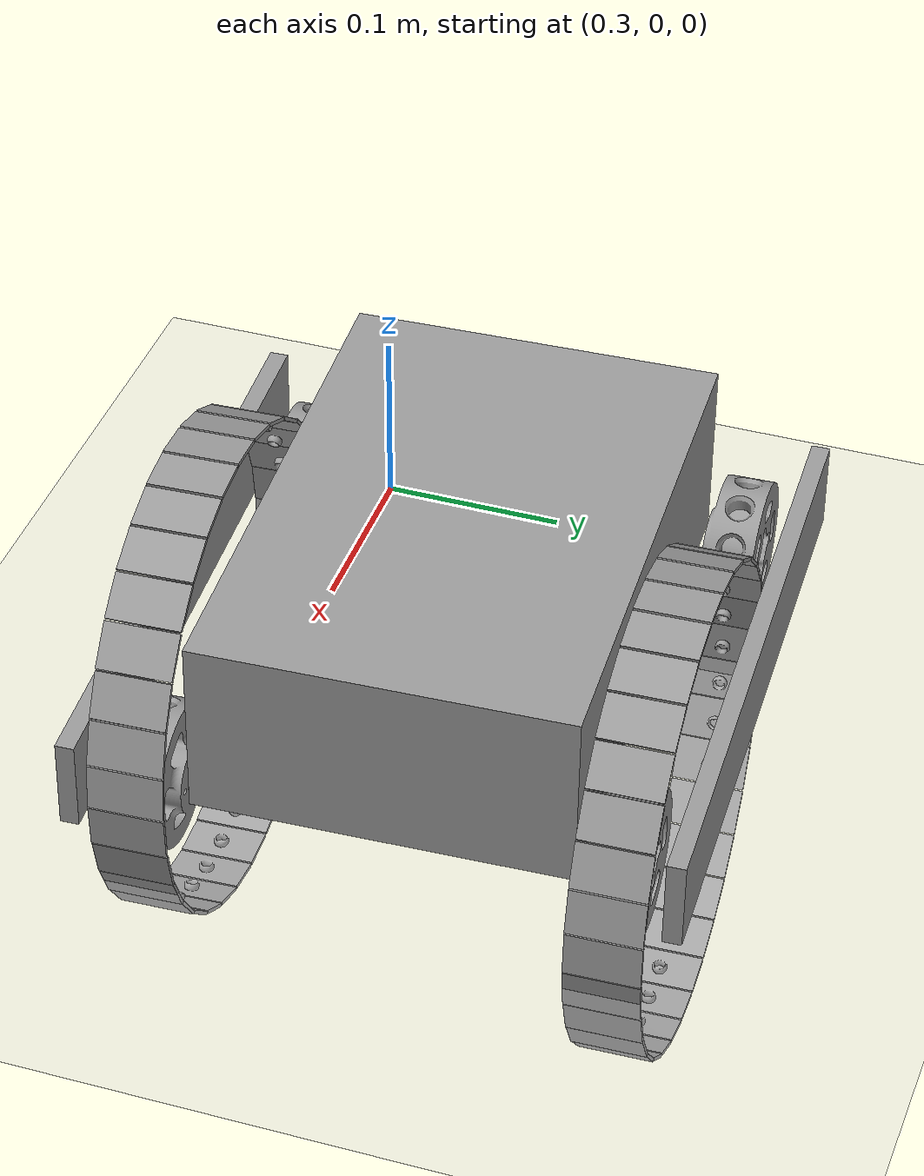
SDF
<sdf version="1.6">
 <world name="default">
  <light name="sun" type="directional">
   <pose>0 0 10 0 -0 0</pose>
   <diffuse>0.8 0.8 0.8 1</diffuse>
   <specular>0.1 0.1 0.1 1</specular>
   <attenuation>
    <range>1000</range>
    <constant>0.9</constant>
    <linear>0.01</linear>
    <quadratic>0.001</quadratic>
   </attenuation>
   <direction>-0.5 0.5 -1</direction>
  </light>
  <model name="ground_plane">
   <static>1</static>
   <link name="link">
    <collision name="collision">
     <geometry><plane><normal>0 0 1</normal><size>100 100</size></plane></geometry>
     <surface><friction><ode><mu>100</mu><mu2>50</mu2></ode></friction></surface>
    </collision>
    <visual name="visual">
     <cast_shadows>0</cast_shadows>
     <geometry><plane><normal>0 0 1</normal><size>100 100</size></plane></geometry>
     <material>
      <script><uri>file://media/materials/scripts/gazebo.material</uri><name>Gazebo/Grey</name></script>
     </material>
    </visual>
   </link>
  </model>
  <gravity>0 0 -9.8</gravity>
  <magnetic_field>6e-06 2.3e-05 -4.2e-05</magnetic_field>
  <atmosphere type="adiabatic"/>
  <physics name="default_physics" default="0" type="ode">
   <max_step_size>0.001</max_step_size>
   <real_time_factor>1</real_time_factor>
   <real_time_update_rate>1000</real_time_update_rate>
  </physics>
  <scene><ambient>0.4 0.4 0.4 1</ambient><background>0.7 0.7 0.7 1</background><shadows>1</shadows></scene>
  <spherical_coordinates>
   <surface_model>EARTH_WGS84</surface_model>
   <latitude_deg>0</latitude_deg>
   <longitude_deg>0</longitude_deg>
   <elevation>0</elevation>
   <heading_deg>0</heading_deg>
  </spherical_coordinates>
  <model name="simple_car">
   <link name="chasis">
    <pose>0 0 0.05 0 -0 0</pose>
    <inertial>
     <mass>1</mass>
     <inertia>
      <ixx>0.166667</ixx>
      <ixy>0</ixy>
      <ixz>0</ixz>
      <iyy>0.166667</iyy>
      <iyz>0</iyz>
      <izz>0.166667</izz>
     </inertia>
    </inertial>
    <visual name="visual">
     <geometry><box><size>0.3 0.2 0.1</size></box></geometry>
     <material>
      <script><name>Gazebo/Grey</name><uri>file://media/materials/scripts/gazebo.material</uri></script>
      <ambient>0.3 0.3 0.3 1</ambient>
      <diffuse>0.7 0.7 0.7 1</diffuse>
      <specular>0.01 0.01 0.01 1</specular>
      <emissive>0 0 0 1</emissive>
      <shader type="vertex"><normal_map>__default__</normal_map></shader>
     </material>
    </visual>
    <collision name="collision"><geometry><box><size>0.3 0.2 0.1</size></box></geometry></collision>
   </link>
   <link name="drum_0">
    <pose>0.13 -0.12 0 1.5707 -0 0</pose>
    <self_collide>1</self_collide>
    <inertial>
     <mass>1</mass>
     <inertia><ixx>1</ixx><ixy>0</ixy><ixz>0</ixz><iyy>1</iyy><iyz>0</iyz><izz>1</izz></inertia>
    </inertial>
    <visual name="visual">
     <pose>-0.0375 -0.0375 -0.034 0 -0 0</pose>
     <geometry>
      <mesh><uri>model://track_drum/meshes/drum.STL</uri><scale>0.001 0.001 0.001</scale></mesh>
     </geometry>
     <material>
      <lighting>1</lighting>
      <script><uri>file://media/materials/scripts/gazebo.material</uri><name>Gazebo/Grey</name></script>
      <ambient>0.3 0.3 0.3 1</ambient>
      <diffuse>0.7 0.7 0.7 1</diffuse>
      <specular>0.01 0.01 0.01 1</specular>
      <emissive>0 0 0 1</emissive>
      <shader type="vertex"><normal_map>__default__</normal_map></shader>
     </material>
    </visual>
    <collision name="collision">
     <max_contacts>20</max_contacts>
     <pose>-0.0375 -0.0375 -0.034 0 -0 0</pose>
     <geometry>
      <mesh><uri>model://track_drum/meshes/drum.STL</uri><scale>0.001 0.001 0.001</scale></mesh>
     </geometry>
     <surface>
      <friction><ode><mu>1</mu><mu2>1</mu2><fdir1>0 0 0</fdir1><slip1>0</slip1><slip2>0</slip2></ode></friction>
      <bounce><restitution_coefficient>0</restitution_coefficient><threshold>1</threshold></bounce>
      <contact>
       <collide_without_contact>0</collide_without_contact>
       <collide_without_contact_bitmask>1</collide_without_contact_bitmask>
       <collide_bitmask>1</collide_bitmask>
       <ode>
        <soft_cfm>0.1</soft_cfm>
        <soft_erp>0.2</soft_erp>
        <kp>1e+13</kp>
        <kd>1</kd>
        <max_vel>0.01</max_vel>
        <min_depth>0</min_depth>
       </ode>
       <bullet>
        <split_impulse>1</split_impulse>
        <split_impulse_penetration_threshold>-0.01</split_impulse_penetration_threshold>
        <soft_cfm>0</soft_cfm>
        <soft_erp>0.2</soft_erp>
        <kp>1e+13</kp>
        <kd>1</kd>
       </bullet>
      </contact>
     </surface>
    </collision>
   </link>
   <link name="drum_1">
    <pose>-0.13 -0.12 0 1.5707 -0 0</pose>
    <self_collide>1</self_collide>
    <inertial>
     <mass>1</mass>
     <inertia><ixx>1</ixx><ixy>0</ixy><ixz>0</ixz><iyy>1</iyy><iyz>0</iyz><izz>1</izz></inertia>
    </inertial>
    <visual name="visual">
     <pose>-0.0375 -0.0375 -0.034 0 -0 0</pose>
     <geometry>
      <mesh><uri>model://track_drum/meshes/drum.STL</uri><scale>0.001 0.001 0.001</scale></mesh>
     </geometry>
     <material>
      <lighting>1</lighting>
      <script><uri>file://media/materials/scripts/gazebo.material</uri><name>Gazebo/Grey</name></script>
      <ambient>0.3 0.3 0.3 1</ambient>
      <diffuse>0.7 0.7 0.7 1</diffuse>
      <specular>0.01 0.01 0.01 1</specular>
      <emissive>0 0 0 1</emissive>
      <shader type="vertex"><normal_map>__default__</normal_map></shader>
     </material>
    </visual>
    <collision name="collision">
     <max_contacts>20</max_contacts>
     <pose>-0.0375 -0.0375 -0.034 0 -0 0</pose>
     <geometry>
      <mesh><uri>model://track_drum/meshes/drum.STL</uri><scale>0.001 0.001 0.001</scale></mesh>
     </geometry>
     <surface>
      <friction><ode><mu>1</mu><mu2>1</mu2><fdir1>0 0 0</fdir1><slip1>0</slip1><slip2>0</slip2></ode></friction>
      <bounce><restitution_coefficient>0</restitution_coefficient><threshold>1</threshold></bounce>
      <contact>
       <collide_without_contact>0</collide_without_contact>
       <collide_without_contact_bitmask>1</collide_without_contact_bitmask>
       <collide_bitmask>1</collide_bitmask>
       <ode>
        <soft_cfm>0.1</soft_cfm>
        <soft_erp>0.2</soft_erp>
        <kp>1e+13</kp>
        <kd>1</kd>
        <max_vel>0.01</max_vel>
        <min_depth>0</min_depth>
       </ode>
       <bullet>
        <split_impulse>1</split_impulse>
        <split_impulse_penetration_threshold>-0.01</split_impulse_penetration_threshold>
        <soft_cfm>0</soft_cfm>
        <soft_erp>0.2</soft_erp>
        <kp>1e+13</kp>
        <kd>1</kd>
       </bullet>
      </contact>
     </surface>
    </collision>
   </link>
   <link name="drum_2">
    <pose>0.13 0.12 0 1.5707 -0 3.14159</pose>
    <self_collide>1</self_collide>
    <inertial>
     <mass>1</mass>
     <inertia><ixx>1</ixx><ixy>0</ixy><ixz>0</ixz><iyy>1</iyy><iyz>0</iyz><izz>1</izz></inertia>
    </inertial>
    <visual name="visual">
     <pose>-0.0375 -0.0375 -0.034 0 -0 0</pose>
     <geometry>
      <mesh><uri>model://track_drum/meshes/drum.STL</uri><scale>0.001 0.001 0.001</scale></mesh>
     </geometry>
     <material>
      <lighting>1</lighting>
      <script><uri>file://media/materials/scripts/gazebo.material</uri><name>Gazebo/Grey</name></script>
      <ambient>0.3 0.3 0.3 1</ambient>
      <diffuse>0.7 0.7 0.7 1</diffuse>
      <specular>0.01 0.01 0.01 1</specular>
      <emissive>0 0 0 1</emissive>
      <shader type="vertex"><normal_map>__default__</normal_map></shader>
     </material>
    </visual>
    <collision name="collision">
     <max_contacts>20</max_contacts>
     <pose>-0.0375 -0.0375 -0.034 0 -0 0</pose>
     <geometry>
      <mesh><uri>model://track_drum/meshes/drum.STL</uri><scale>0.001 0.001 0.001</scale></mesh>
     </geometry>
     <surface>
      <friction><ode><mu>1</mu><mu2>1</mu2><fdir1>0 0 0</fdir1><slip1>0</slip1><slip2>0</slip2></ode></friction>
      <bounce><restitution_coefficient>0</restitution_coefficient><threshold>1</threshold></bounce>
      <contact>
       <collide_without_contact>0</collide_without_contact>
       <collide_without_contact_bitmask>1</collide_without_contact_bitmask>
       <collide_bitmask>1</collide_bitmask>
       <ode>
        <soft_cfm>0.1</soft_cfm>
        <soft_erp>0.2</soft_erp>
        <kp>1e+13</kp>
        <kd>1</kd>
        <max_vel>0.01</max_vel>
        <min_depth>0</min_depth>
       </ode>
       <bullet>
        <split_impulse>1</split_impulse>
        <split_impulse_penetration_threshold>-0.01</split_impulse_penetration_threshold>
        <soft_cfm>0</soft_cfm>
        <soft_erp>0.2</soft_erp>
        <kp>1e+13</kp>
        <kd>1</kd>
       </bullet>
      </contact>
     </surface>
    </collision>
   </link>
   <link name="drum_3">
    <pose>-0.13 0.12 0 1.5707 -0 3.14159</pose>
    <self_collide>1</self_collide>
    <inertial>
     <mass>1</mass>
     <inertia><ixx>1</ixx><ixy>0</ixy><ixz>0</ixz><iyy>1</iyy><iyz>0</iyz><izz>1</izz></inertia>
    </inertial>
    <visual name="visual">
     <pose>-0.0375 -0.0375 -0.034 0 -0 0</pose>
     <geometry>
      <mesh><uri>model://track_drum/meshes/drum.STL</uri><scale>0.001 0.001 0.001</scale></mesh>
     </geometry>
     <material>
      <lighting>1</lighting>
      <script><uri>file://media/materials/scripts/gazebo.material</uri><name>Gazebo/Grey</name></script>
      <ambient>0.3 0.3 0.3 1</ambient>
      <diffuse>0.7 0.7 0.7 1</diffuse>
      <specular>0.01 0.01 0.01 1</specular>
      <emissive>0 0 0 1</emissive>
      <shader type="vertex"><normal_map>__default__</normal_map></shader>
     </material>
    </visual>
    <collision name="collision">
     <max_contacts>20</max_contacts>
     <pose>-0.0375 -0.0375 -0.034 0 -0 0</pose>
     <geometry>
      <mesh><uri>model://track_drum/meshes/drum.STL</uri><scale>0.001 0.001 0.001</scale></mesh>
     </geometry>
     <surface>
      <friction><ode><mu>1</mu><mu2>1</mu2><fdir1>0 0 0</fdir1><slip1>0</slip1><slip2>0</slip2></ode></friction>
      <bounce><restitution_coefficient>0</restitution_coefficient><threshold>1</threshold></bounce>
      <contact>
       <collide_without_contact>0</collide_without_contact>
       <collide_without_contact_bitmask>1</collide_without_contact_bitmask>
       <collide_bitmask>1</collide_bitmask>
       <ode>
        <soft_cfm>0.1</soft_cfm>
        <soft_erp>0.2</soft_erp>
        <kp>1e+13</kp>
        <kd>1</kd>
        <max_vel>0.01</max_vel>
        <min_depth>0</min_depth>
       </ode>
       <bullet>
        <split_impulse>1</split_impulse>
        <split_impulse_penetration_threshold>-0.01</split_impulse_penetration_threshold>
        <soft_cfm>0</soft_cfm>
        <soft_erp>0.2</soft_erp>
        <kp>1e+13</kp>
        <kd>1</kd>
       </bullet>
      </contact>
     </surface>
    </collision>
   </link>
   <link name="left_block">
    <pose>0 -0.155 0.02 0 -0 0</pose>
    <inertial>
     <mass>1</mass>
     <inertia>
      <ixx>0.166667</ixx>
      <ixy>0</ixy>
      <ixz>0</ixz>
      <iyy>0.166667</iyy>
      <iyz>0</iyz>
      <izz>0.166667</izz>
     </inertia>
    </inertial>
    <visual name="visual">
     <geometry><box><size>0.35 0.01 0.05</size></box></geometry>
     <material>
      <script><name>Gazebo/Grey</name><uri>file://media/materials/scripts/gazebo.material</uri></script>
      <ambient>0.3 0.3 0.3 1</ambient>
      <diffuse>0.7 0.7 0.7 1</diffuse>
      <specular>0.01 0.01 0.01 1</specular>
      <emissive>0 0 0 1</emissive>
      <shader type="vertex"><normal_map>__default__</normal_map></shader>
     </material>
    </visual>
    <collision name="collision"><geometry><box><size>0.35 0.01 0.05</size></box></geometry></collision>
   </link>
   <link name="right_block">
    <pose>0 0.155 0.02 0 -0 0</pose>
    <inertial>
     <mass>1</mass>
     <inertia>
      <ixx>0.166667</ixx>
      <ixy>0</ixy>
      <ixz>0</ixz>
      <iyy>0.166667</iyy>
      <iyz>0</iyz>
      <izz>0.166667</izz>
     </inertia>
    </inertial>
    <visual name="visual">
     <geometry><box><size>0.35 0.01 0.05</size></box></geometry>
     <material>
      <script><name>Gazebo/Grey</name><uri>file://media/materials/scripts/gazebo.material</uri></script>
      <ambient>0.3 0.3 0.3 1</ambient>
      <diffuse>0.7 0.7 0.7 1</diffuse>
      <specular>0.01 0.01 0.01 1</specular>
      <emissive>0 0 0 1</emissive>
      <shader type="vertex"><normal_map>__default__</normal_map></shader>
     </material>
    </visual>
    <collision name="collision"><geometry><box><size>0.35 0.01 0.05</size></box></geometry></collision>
   </link>
   <joint name="left_block_joint" type="fixed">
    <child>left_block</child>
    <parent>chasis</parent>
    <axis>
     <xyz>0 0 1</xyz>
     <use_parent_model_frame>0</use_parent_model_frame>
     <limit><lower>-1e+16</lower><upper>1e+16</upper></limit>
    </axis>
   </joint>
   <joint name="right_block_joint" type="fixed">
    <child>right_block</child>
    <parent>chasis</parent>
    <axis>
     <xyz>0 0 1</xyz>
     <use_parent_model_frame>0</use_parent_model_frame>
     <limit><lower>-1e+16</lower><upper>1e+16</upper></limit>
    </axis>
   </joint>
   <joint name="joint_0" type="revolute">
    <pose>0 0 -0.015 0 -0 0</pose>
    <child>drum_0</child>
    <parent>chasis</parent>
    <axis>
     <xyz>0 0 1</xyz>
     <use_parent_model_frame>0</use_parent_model_frame>
     <limit><lower>-1e+16</lower><upper>1e+16</upper></limit>
     <dynamics><spring_reference>0</spring_reference><spring_stiffness>0</spring_stiffness></dynamics>
    </axis>
   </joint>
   <joint name="joint_1" type="revolute">
    <pose>0 0 -0.015 0 -0 0</pose>
    <child>drum_1</child>
    <parent>chasis</parent>
    <axis>
     <xyz>0 0 1</xyz>
     <use_parent_model_frame>0</use_parent_model_frame>
     <limit><lower>-1e+16</lower><upper>1e+16</upper></limit>
     <dynamics><spring_reference>0</spring_reference><spring_stiffness>0</spring_stiffness></dynamics>
    </axis>
   </joint>
   <joint name="joint_2" type="revolute">
    <pose>0 0 -0.015 0 -0 0</pose>
    <child>drum_2</child>
    <parent>chasis</parent>
    <axis>
     <xyz>0 0 1</xyz>
     <use_parent_model_frame>0</use_parent_model_frame>
     <limit><lower>-1e+16</lower><upper>1e+16</upper></limit>
     <dynamics><spring_reference>0</spring_reference><spring_stiffness>0</spring_stiffness></dynamics>
    </axis>
   </joint>
   <joint name="joint_3" type="revolute">
    <pose>0 0 -0.015 0 -0 0</pose>
    <child>drum_3</child>
    <parent>chasis</parent>
    <axis>
     <xyz>0 0 1</xyz>
     <use_parent_model_frame>0</use_parent_model_frame>
     <limit><lower>-1e+16</lower><upper>1e+16</upper></limit>
     <dynamics><spring_reference>0</spring_reference><spring_stiffness>0</spring_stiffness></dynamics>
    </axis>
   </joint>
   <static>0</static>
   <pose>0.487877 0.106161 0.049283 -0.013098 0.000921 0.056337</pose>
  </model>
  <model name="track_2">
   <static>0</static>
   <pose>0.539187 -0.014415 0.05516 -1.5696 0.043693 0.04388</pose>
   <link name="link_0">
    <pose>0.1309 0 0 -1.5708 0 1.5708</pose>
    <inertial>
     <mass>1</mass>
     <inertia>
      <ixx>0.166667</ixx>
      <ixy>0</ixy>
      <ixz>0</ixz>
      <iyy>0.166667</iyy>
      <iyz>0</iyz>
      <izz>0.166667</izz>
     </inertia>
    </inertial>
    <visual name="visual">
     <geometry><mesh><uri>model://track_thread/meshes/CP1.dae</uri><scale>1 1 1</scale></mesh></geometry>
     <material>
      <lighting>1</lighting>
      <script><uri>file://media/materials/scripts/gazebo.material</uri><name>Gazebo/Grey</name></script>
      <ambient>0.3 0.3 0.3 1</ambient>
      <diffuse>0.7 0.7 0.7 1</diffuse>
      <specular>0.01 0.01 0.01 1</specular>
      <emissive>0 0 0 1</emissive>
      <shader type="vertex"><normal_map>__default__</normal_map></shader>
     </material>
    </visual>
    <collision name="collision">
     <geometry><mesh><uri>model://track_thread/meshes/CP1.dae</uri><scale>1 1 1</scale></mesh></geometry>
    </collision>
   </link>
   <link name="link_1">
    <pose>0.1285 0.0248 0 -1.5708 -0 1.7612</pose>
    <inertial>
     <mass>1</mass>
     <inertia>
      <ixx>0.166667</ixx>
      <ixy>0</ixy>
      <ixz>0</ixz>
      <iyy>0.166667</iyy>
      <iyz>0</iyz>
      <izz>0.166667</izz>
     </inertia>
    </inertial>
    <visual name="visual">
     <geometry><mesh><uri>model://track_thread/meshes/CP1.dae</uri><scale>1 1 1</scale></mesh></geometry>
     <material>
      <lighting>1</lighting>
      <script><uri>file://media/materials/scripts/gazebo.material</uri><name>Gazebo/Grey</name></script>
      <ambient>0.3 0.3 0.3 1</ambient>
      <diffuse>0.7 0.7 0.7 1</diffuse>
      <specular>0.01 0.01 0.01 1</specular>
      <emissive>0 0 0 1</emissive>
      <shader type="vertex"><normal_map>__default__</normal_map></shader>
     </material>
    </visual>
    <collision name="collision">
     <geometry><mesh><uri>model://track_thread/meshes/CP1.dae</uri><scale>1 1 1</scale></mesh></geometry>
    </collision>
   </link>
   <link name="link_2">
    <pose>0.1215 0.0487 0 -1.5708 -0 1.9516</pose>
    <inertial>
     <mass>1</mass>
     <inertia>
      <ixx>0.166667</ixx>
      <ixy>0</ixy>
      <ixz>0</ixz>
      <iyy>0.166667</iyy>
      <iyz>0</iyz>
      <izz>0.166667</izz>
     </inertia>
    </inertial>
    <visual name="visual">
     <geometry><mesh><uri>model://track_thread/meshes/CP1.dae</uri><scale>1 1 1</scale></mesh></geometry>
     <material>
      <lighting>1</lighting>
      <script><uri>file://media/materials/scripts/gazebo.material</uri><name>Gazebo/Grey</name></script>
      <ambient>0.3 0.3 0.3 1</ambient>
      <diffuse>0.7 0.7 0.7 1</diffuse>
      <specular>0.01 0.01 0.01 1</specular>
      <emissive>0 0 0 1</emissive>
      <shader type="vertex"><normal_map>__default__</normal_map></shader>
     </material>
    </visual>
    <collision name="collision">
     <geometry><mesh><uri>model://track_thread/meshes/CP1.dae</uri><scale>1 1 1</scale></mesh></geometry>
    </collision>
   </link>
   <link name="link_3">
    <pose>0.1101 0.0708 0 -1.5708 -0 2.142</pose>
    <inertial>
     <mass>1</mass>
     <inertia>
      <ixx>0.166667</ixx>
      <ixy>0</ixy>
      <ixz>0</ixz>
      <iyy>0.166667</iyy>
      <iyz>0</iyz>
      <izz>0.166667</izz>
     </inertia>
    </inertial>
    <visual name="visual">
     <geometry><mesh><uri>model://track_thread/meshes/CP1.dae</uri><scale>1 1 1</scale></mesh></geometry>
     <material>
      <lighting>1</lighting>
      <script><uri>file://media/materials/scripts/gazebo.material</uri><name>Gazebo/Grey</name></script>
      <ambient>0.3 0.3 0.3 1</ambient>
      <diffuse>0.7 0.7 0.7 1</diffuse>
      <specular>0.01 0.01 0.01 1</specular>
      <emissive>0 0 0 1</emissive>
      <shader type="vertex"><normal_map>__default__</normal_map></shader>
     </material>
    </visual>
    <collision name="collision">
     <geometry><mesh><uri>model://track_thread/meshes/CP1.dae</uri><scale>1 1 1</scale></mesh></geometry>
    </collision>
   </link>
   <link name="link_4">
    <pose>0.0947 0.0903 0 -1.5708 -0 2.3324</pose>
    <inertial>
     <mass>1</mass>
     <inertia>
      <ixx>0.166667</ixx>
      <ixy>0</ixy>
      <ixz>0</ixz>
      <iyy>0.166667</iyy>
      <iyz>0</iyz>
      <izz>0.166667</izz>
     </inertia>
    </inertial>
    <visual name="visual">
     <geometry><mesh><uri>model://track_thread/meshes/CP1.dae</uri><scale>1 1 1</scale></mesh></geometry>
     <material>
      <lighting>1</lighting>
      <script><uri>file://media/materials/scripts/gazebo.material</uri><name>Gazebo/Grey</name></script>
      <ambient>0.3 0.3 0.3 1</ambient>
      <diffuse>0.7 0.7 0.7 1</diffuse>
      <specular>0.01 0.01 0.01 1</specular>
      <emissive>0 0 0 1</emissive>
      <shader type="vertex"><normal_map>__default__</normal_map></shader>
     </material>
    </visual>
    <collision name="collision">
     <geometry><mesh><uri>model://track_thread/meshes/CP1.dae</uri><scale>1 1 1</scale></mesh></geometry>
    </collision>
   </link>
   <link name="link_5">
    <pose>0.0759 0.1066 0 -1.5708 0 2.5228</pose>
    <inertial>
     <mass>1</mass>
     <inertia>
      <ixx>0.166667</ixx>
      <ixy>0</ixy>
      <ixz>0</ixz>
      <iyy>0.166667</iyy>
      <iyz>0</iyz>
      <izz>0.166667</izz>
     </inertia>
    </inertial>
    <visual name="visual">
     <geometry><mesh><uri>model://track_thread/meshes/CP1.dae</uri><scale>1 1 1</scale></mesh></geometry>
     <material>
      <lighting>1</lighting>
      <script><uri>file://media/materials/scripts/gazebo.material</uri><name>Gazebo/Grey</name></script>
      <ambient>0.3 0.3 0.3 1</ambient>
      <diffuse>0.7 0.7 0.7 1</diffuse>
      <specular>0.01 0.01 0.01 1</specular>
      <emissive>0 0 0 1</emissive>
      <shader type="vertex"><normal_map>__default__</normal_map></shader>
     </material>
    </visual>
    <collision name="collision">
     <geometry><mesh><uri>model://track_thread/meshes/CP1.dae</uri><scale>1 1 1</scale></mesh></geometry>
    </collision>
   </link>
   <link name="link_6">
    <pose>0.0544 0.1191 0 -1.5708 -0 2.7132</pose>
    <inertial>
     <mass>1</mass>
     <inertia>
      <ixx>0.166667</ixx>
      <ixy>0</ixy>
      <ixz>0</ixz>
      <iyy>0.166667</iyy>
      <iyz>0</iyz>
      <izz>0.166667</izz>
     </inertia>
    </inertial>
    <visual name="visual">
     <geometry><mesh><uri>model://track_thread/meshes/CP1.dae</uri><scale>1 1 1</scale></mesh></geometry>
     <material>
      <lighting>1</lighting>
      <script><uri>file://media/materials/scripts/gazebo.material</uri><name>Gazebo/Grey</name></script>
      <ambient>0.3 0.3 0.3 1</ambient>
      <diffuse>0.7 0.7 0.7 1</diffuse>
      <specular>0.01 0.01 0.01 1</specular>
      <emissive>0 0 0 1</emissive>
      <shader type="vertex"><normal_map>__default__</normal_map></shader>
     </material>
    </visual>
    <collision name="collision">
     <geometry><mesh><uri>model://track_thread/meshes/CP1.dae</uri><scale>1 1 1</scale></mesh></geometry>
    </collision>
   </link>
   <link name="link_7">
    <pose>0.0309 0.1272 0 -1.5708 -0 2.9036</pose>
    <inertial>
     <mass>1</mass>
     <inertia>
      <ixx>0.166667</ixx>
      <ixy>0</ixy>
      <ixz>0</ixz>
      <iyy>0.166667</iyy>
      <iyz>0</iyz>
      <izz>0.166667</izz>
     </inertia>
    </inertial>
    <visual name="visual">
     <geometry><mesh><uri>model://track_thread/meshes/CP1.dae</uri><scale>1 1 1</scale></mesh></geometry>
     <material>
      <lighting>1</lighting>
      <script><uri>file://media/materials/scripts/gazebo.material</uri><name>Gazebo/Grey</name></script>
      <ambient>0.3 0.3 0.3 1</ambient>
      <diffuse>0.7 0.7 0.7 1</diffuse>
      <specular>0.01 0.01 0.01 1</specular>
      <emissive>0 0 0 1</emissive>
      <shader type="vertex"><normal_map>__default__</normal_map></shader>
     </material>
    </visual>
    <collision name="collision">
     <geometry><mesh><uri>model://track_thread/meshes/CP1.dae</uri><scale>1 1 1</scale></mesh></geometry>
    </collision>
   </link>
   <link name="link_8">
    <pose>0.0062 0.1308 0 -1.5708 -0 3.094</pose>
    <inertial>
     <mass>1</mass>
     <inertia>
      <ixx>0.166667</ixx>
      <ixy>0</ixy>
      <ixz>0</ixz>
      <iyy>0.166667</iyy>
      <iyz>0</iyz>
      <izz>0.166667</izz>
     </inertia>
    </inertial>
    <visual name="visual">
     <geometry><mesh><uri>model://track_thread/meshes/CP1.dae</uri><scale>1 1 1</scale></mesh></geometry>
     <material>
      <lighting>1</lighting>
      <script><uri>file://media/materials/scripts/gazebo.material</uri><name>Gazebo/Grey</name></script>
      <ambient>0.3 0.3 0.3 1</ambient>
      <diffuse>0.7 0.7 0.7 1</diffuse>
      <specular>0.01 0.01 0.01 1</specular>
      <emissive>0 0 0 1</emissive>
      <shader type="vertex"><normal_map>__default__</normal_map></shader>
     </material>
    </visual>
    <collision name="collision">
     <geometry><mesh><uri>model://track_thread/meshes/CP1.dae</uri><scale>1 1 1</scale></mesh></geometry>
    </collision>
   </link>
   <link name="link_9">
    <pose>-0.0186 0.1296 0 -1.5708 0 -2.99878</pose>
    <inertial>
     <mass>1</mass>
     <inertia>
      <ixx>0.166667</ixx>
      <ixy>0</ixy>
      <ixz>0</ixz>
      <iyy>0.166667</iyy>
      <iyz>0</iyz>
      <izz>0.166667</izz>
     </inertia>
    </inertial>
    <visual name="visual">
     <geometry><mesh><uri>model://track_thread/meshes/CP1.dae</uri><scale>1 1 1</scale></mesh></geometry>
     <material>
      <lighting>1</lighting>
      <script><uri>file://media/materials/scripts/gazebo.material</uri><name>Gazebo/Grey</name></script>
      <ambient>0.3 0.3 0.3 1</ambient>
      <diffuse>0.7 0.7 0.7 1</diffuse>
      <specular>0.01 0.01 0.01 1</specular>
      <emissive>0 0 0 1</emissive>
      <shader type="vertex"><normal_map>__default__</normal_map></shader>
     </material>
    </visual>
    <collision name="collision">
     <geometry><mesh><uri>model://track_thread/meshes/CP1.dae</uri><scale>1 1 1</scale></mesh></geometry>
    </collision>
   </link>
   <link name="link_10">
    <pose>-0.0428 0.1237 0 -1.5708 -0 -2.80838</pose>
    <inertial>
     <mass>1</mass>
     <inertia>
      <ixx>0.166667</ixx>
      <ixy>0</ixy>
      <ixz>0</ixz>
      <iyy>0.166667</iyy>
      <iyz>0</iyz>
      <izz>0.166667</izz>
     </inertia>
    </inertial>
    <visual name="visual">
     <geometry><mesh><uri>model://track_thread/meshes/CP1.dae</uri><scale>1 1 1</scale></mesh></geometry>
     <material>
      <lighting>1</lighting>
      <script><uri>file://media/materials/scripts/gazebo.material</uri><name>Gazebo/Grey</name></script>
      <ambient>0.3 0.3 0.3 1</ambient>
      <diffuse>0.7 0.7 0.7 1</diffuse>
      <specular>0.01 0.01 0.01 1</specular>
      <emissive>0 0 0 1</emissive>
      <shader type="vertex"><normal_map>__default__</normal_map></shader>
     </material>
    </visual>
    <collision name="collision">
     <geometry><mesh><uri>model://track_thread/meshes/CP1.dae</uri><scale>1 1 1</scale></mesh></geometry>
    </collision>
   </link>
   <link name="link_11">
    <pose>-0.0655 0.1134 0 -1.5708 -0 -2.61799</pose>
    <inertial>
     <mass>1</mass>
     <inertia>
      <ixx>0.166667</ixx>
      <ixy>0</ixy>
      <ixz>0</ixz>
      <iyy>0.166667</iyy>
      <iyz>0</iyz>
      <izz>0.166667</izz>
     </inertia>
    </inertial>
    <visual name="visual">
     <geometry><mesh><uri>model://track_thread/meshes/CP1.dae</uri><scale>1 1 1</scale></mesh></geometry>
     <material>
      <lighting>1</lighting>
      <script><uri>file://media/materials/scripts/gazebo.material</uri><name>Gazebo/Grey</name></script>
      <ambient>0.3 0.3 0.3 1</ambient>
      <diffuse>0.7 0.7 0.7 1</diffuse>
      <specular>0.01 0.01 0.01 1</specular>
      <emissive>0 0 0 1</emissive>
      <shader type="vertex"><normal_map>__default__</normal_map></shader>
     </material>
    </visual>
    <collision name="collision">
     <geometry><mesh><uri>model://track_thread/meshes/CP1.dae</uri><scale>1 1 1</scale></mesh></geometry>
    </collision>
   </link>
   <link name="link_12">
    <pose>-0.0857 0.0989 0 -1.5708 -0 -2.42759</pose>
    <inertial>
     <mass>1</mass>
     <inertia>
      <ixx>0.166667</ixx>
      <ixy>0</ixy>
      <ixz>0</ixz>
      <iyy>0.166667</iyy>
      <iyz>0</iyz>
      <izz>0.166667</izz>
     </inertia>
    </inertial>
    <visual name="visual">
     <geometry><mesh><uri>model://track_thread/meshes/CP1.dae</uri><scale>1 1 1</scale></mesh></geometry>
     <material>
      <lighting>1</lighting>
      <script><uri>file://media/materials/scripts/gazebo.material</uri><name>Gazebo/Grey</name></script>
      <ambient>0.3 0.3 0.3 1</ambient>
      <diffuse>0.7 0.7 0.7 1</diffuse>
      <specular>0.01 0.01 0.01 1</specular>
      <emissive>0 0 0 1</emissive>
      <shader type="vertex"><normal_map>__default__</normal_map></shader>
     </material>
    </visual>
    <collision name="collision">
     <geometry><mesh><uri>model://track_thread/meshes/CP1.dae</uri><scale>1 1 1</scale></mesh></geometry>
    </collision>
   </link>
   <link name="link_13">
    <pose>-0.1029 0.0809 0 -1.5708 -0 -2.23719</pose>
    <inertial>
     <mass>1</mass>
     <inertia>
      <ixx>0.166667</ixx>
      <ixy>0</ixy>
      <ixz>0</ixz>
      <iyy>0.166667</iyy>
      <iyz>0</iyz>
      <izz>0.166667</izz>
     </inertia>
    </inertial>
    <visual name="visual">
     <geometry><mesh><uri>model://track_thread/meshes/CP1.dae</uri><scale>1 1 1</scale></mesh></geometry>
     <material>
      <lighting>1</lighting>
      <script><uri>file://media/materials/scripts/gazebo.material</uri><name>Gazebo/Grey</name></script>
      <ambient>0.3 0.3 0.3 1</ambient>
      <diffuse>0.7 0.7 0.7 1</diffuse>
      <specular>0.01 0.01 0.01 1</specular>
      <emissive>0 0 0 1</emissive>
      <shader type="vertex"><normal_map>__default__</normal_map></shader>
     </material>
    </visual>
    <collision name="collision">
     <geometry><mesh><uri>model://track_thread/meshes/CP1.dae</uri><scale>1 1 1</scale></mesh></geometry>
    </collision>
   </link>
   <link name="link_14">
    <pose>-0.1164 0.06 0 -1.5708 -0 -2.04678</pose>
    <inertial>
     <mass>1</mass>
     <inertia>
      <ixx>0.166667</ixx>
      <ixy>0</ixy>
      <ixz>0</ixz>
      <iyy>0.166667</iyy>
      <iyz>0</iyz>
      <izz>0.166667</izz>
     </inertia>
    </inertial>
    <visual name="visual">
     <geometry><mesh><uri>model://track_thread/meshes/CP1.dae</uri><scale>1 1 1</scale></mesh></geometry>
     <material>
      <lighting>1</lighting>
      <script><uri>file://media/materials/scripts/gazebo.material</uri><name>Gazebo/Grey</name></script>
      <ambient>0.3 0.3 0.3 1</ambient>
      <diffuse>0.7 0.7 0.7 1</diffuse>
      <specular>0.01 0.01 0.01 1</specular>
      <emissive>0 0 0 1</emissive>
      <shader type="vertex"><normal_map>__default__</normal_map></shader>
     </material>
    </visual>
    <collision name="collision">
     <geometry><mesh><uri>model://track_thread/meshes/CP1.dae</uri><scale>1 1 1</scale></mesh></geometry>
    </collision>
   </link>
   <link name="link_15">
    <pose>-0.1256 0.0369 0 -1.5708 -0 -1.85638</pose>
    <inertial>
     <mass>1</mass>
     <inertia>
      <ixx>0.166667</ixx>
      <ixy>0</ixy>
      <ixz>0</ixz>
      <iyy>0.166667</iyy>
      <iyz>0</iyz>
      <izz>0.166667</izz>
     </inertia>
    </inertial>
    <visual name="visual">
     <geometry><mesh><uri>model://track_thread/meshes/CP1.dae</uri><scale>1 1 1</scale></mesh></geometry>
     <material>
      <lighting>1</lighting>
      <script><uri>file://media/materials/scripts/gazebo.material</uri><name>Gazebo/Grey</name></script>
      <ambient>0.3 0.3 0.3 1</ambient>
      <diffuse>0.7 0.7 0.7 1</diffuse>
      <specular>0.01 0.01 0.01 1</specular>
      <emissive>0 0 0 1</emissive>
      <shader type="vertex"><normal_map>__default__</normal_map></shader>
     </material>
    </visual>
    <collision name="collision">
     <geometry><mesh><uri>model://track_thread/meshes/CP1.dae</uri><scale>1 1 1</scale></mesh></geometry>
    </collision>
   </link>
   <link name="link_16">
    <pose>-0.1303 0.0124 0 -1.5708 0 -1.66599</pose>
    <inertial>
     <mass>1</mass>
     <inertia>
      <ixx>0.166667</ixx>
      <ixy>0</ixy>
      <ixz>0</ixz>
      <iyy>0.166667</iyy>
      <iyz>0</iyz>
      <izz>0.166667</izz>
     </inertia>
    </inertial>
    <visual name="visual">
     <geometry><mesh><uri>model://track_thread/meshes/CP1.dae</uri><scale>1 1 1</scale></mesh></geometry>
     <material>
      <lighting>1</lighting>
      <script><uri>file://media/materials/scripts/gazebo.material</uri><name>Gazebo/Grey</name></script>
      <ambient>0.3 0.3 0.3 1</ambient>
      <diffuse>0.7 0.7 0.7 1</diffuse>
      <specular>0.01 0.01 0.01 1</specular>
      <emissive>0 0 0 1</emissive>
      <shader type="vertex"><normal_map>__default__</normal_map></shader>
     </material>
    </visual>
    <collision name="collision">
     <geometry><mesh><uri>model://track_thread/meshes/CP1.dae</uri><scale>1 1 1</scale></mesh></geometry>
    </collision>
   </link>
   <link name="link_17">
    <pose>-0.1303 -0.0124 0 -1.5708 0 -1.47558</pose>
    <inertial>
     <mass>1</mass>
     <inertia>
      <ixx>0.166667</ixx>
      <ixy>0</ixy>
      <ixz>0</ixz>
      <iyy>0.166667</iyy>
      <iyz>0</iyz>
      <izz>0.166667</izz>
     </inertia>
    </inertial>
    <visual name="visual">
     <geometry><mesh><uri>model://track_thread/meshes/CP1.dae</uri><scale>1 1 1</scale></mesh></geometry>
     <material>
      <lighting>1</lighting>
      <script><uri>file://media/materials/scripts/gazebo.material</uri><name>Gazebo/Grey</name></script>
      <ambient>0.3 0.3 0.3 1</ambient>
      <diffuse>0.7 0.7 0.7 1</diffuse>
      <specular>0.01 0.01 0.01 1</specular>
      <emissive>0 0 0 1</emissive>
      <shader type="vertex"><normal_map>__default__</normal_map></shader>
     </material>
    </visual>
    <collision name="collision">
     <geometry><mesh><uri>model://track_thread/meshes/CP1.dae</uri><scale>1 1 1</scale></mesh></geometry>
    </collision>
   </link>
   <link name="link_18">
    <pose>-0.1256 -0.0369 0 -1.5708 -0 -1.28519</pose>
    <inertial>
     <mass>1</mass>
     <inertia>
      <ixx>0.166667</ixx>
      <ixy>0</ixy>
      <ixz>0</ixz>
      <iyy>0.166667</iyy>
      <iyz>0</iyz>
      <izz>0.166667</izz>
     </inertia>
    </inertial>
    <visual name="visual">
     <geometry><mesh><uri>model://track_thread/meshes/CP1.dae</uri><scale>1 1 1</scale></mesh></geometry>
     <material>
      <lighting>1</lighting>
      <script><uri>file://media/materials/scripts/gazebo.material</uri><name>Gazebo/Grey</name></script>
      <ambient>0.3 0.3 0.3 1</ambient>
      <diffuse>0.7 0.7 0.7 1</diffuse>
      <specular>0.01 0.01 0.01 1</specular>
      <emissive>0 0 0 1</emissive>
      <shader type="vertex"><normal_map>__default__</normal_map></shader>
     </material>
    </visual>
    <collision name="collision">
     <geometry><mesh><uri>model://track_thread/meshes/CP1.dae</uri><scale>1 1 1</scale></mesh></geometry>
    </collision>
   </link>
   <link name="link_19">
    <pose>-0.1164 -0.06 0 -1.5708 -0 -1.09478</pose>
    <inertial>
     <mass>1</mass>
     <inertia>
      <ixx>0.166667</ixx>
      <ixy>0</ixy>
      <ixz>0</ixz>
      <iyy>0.166667</iyy>
      <iyz>0</iyz>
      <izz>0.166667</izz>
     </inertia>
    </inertial>
    <visual name="visual">
     <geometry><mesh><uri>model://track_thread/meshes/CP1.dae</uri><scale>1 1 1</scale></mesh></geometry>
     <material>
      <lighting>1</lighting>
      <script><uri>file://media/materials/scripts/gazebo.material</uri><name>Gazebo/Grey</name></script>
      <ambient>0.3 0.3 0.3 1</ambient>
      <diffuse>0.7 0.7 0.7 1</diffuse>
      <specular>0.01 0.01 0.01 1</specular>
      <emissive>0 0 0 1</emissive>
      <shader type="vertex"><normal_map>__default__</normal_map></shader>
     </material>
    </visual>
    <collision name="collision">
     <geometry><mesh><uri>model://track_thread/meshes/CP1.dae</uri><scale>1 1 1</scale></mesh></geometry>
    </collision>
   </link>
   <link name="link_20">
    <pose>-0.1029 -0.0809 0 -1.5708 -0 -0.904385</pose>
    <inertial>
     <mass>1</mass>
     <inertia>
      <ixx>0.166667</ixx>
      <ixy>0</ixy>
      <ixz>0</ixz>
      <iyy>0.166667</iyy>
      <iyz>0</iyz>
      <izz>0.166667</izz>
     </inertia>
    </inertial>
    <visual name="visual">
     <geometry><mesh><uri>model://track_thread/meshes/CP1.dae</uri><scale>1 1 1</scale></mesh></geometry>
     <material>
      <lighting>1</lighting>
      <script><uri>file://media/materials/scripts/gazebo.material</uri><name>Gazebo/Grey</name></script>
      <ambient>0.3 0.3 0.3 1</ambient>
      <diffuse>0.7 0.7 0.7 1</diffuse>
      <specular>0.01 0.01 0.01 1</specular>
      <emissive>0 0 0 1</emissive>
      <shader type="vertex"><normal_map>__default__</normal_map></shader>
     </material>
    </visual>
    <collision name="collision">
     <geometry><mesh><uri>model://track_thread/meshes/CP1.dae</uri><scale>1 1 1</scale></mesh></geometry>
    </collision>
   </link>
   <link name="link_21">
    <pose>-0.0857 -0.0989 0 -1.5708 -0 -0.713985</pose>
    <inertial>
     <mass>1</mass>
     <inertia>
      <ixx>0.166667</ixx>
      <ixy>0</ixy>
      <ixz>0</ixz>
      <iyy>0.166667</iyy>
      <iyz>0</iyz>
      <izz>0.166667</izz>
     </inertia>
    </inertial>
    <visual name="visual">
     <geometry><mesh><uri>model://track_thread/meshes/CP1.dae</uri><scale>1 1 1</scale></mesh></geometry>
     <material>
      <lighting>1</lighting>
      <script><uri>file://media/materials/scripts/gazebo.material</uri><name>Gazebo/Grey</name></script>
      <ambient>0.3 0.3 0.3 1</ambient>
      <diffuse>0.7 0.7 0.7 1</diffuse>
      <specular>0.01 0.01 0.01 1</specular>
      <emissive>0 0 0 1</emissive>
      <shader type="vertex"><normal_map>__default__</normal_map></shader>
     </material>
    </visual>
    <collision name="collision">
     <geometry><mesh><uri>model://track_thread/meshes/CP1.dae</uri><scale>1 1 1</scale></mesh></geometry>
    </collision>
   </link>
   <link name="link_22">
    <pose>-0.0655 -0.1134 0 -1.5708 -0 -0.523585</pose>
    <inertial>
     <mass>1</mass>
     <inertia>
      <ixx>0.166667</ixx>
      <ixy>0</ixy>
      <ixz>0</ixz>
      <iyy>0.166667</iyy>
      <iyz>0</iyz>
      <izz>0.166667</izz>
     </inertia>
    </inertial>
    <visual name="visual">
     <geometry><mesh><uri>model://track_thread/meshes/CP1.dae</uri><scale>1 1 1</scale></mesh></geometry>
     <material>
      <lighting>1</lighting>
      <script><uri>file://media/materials/scripts/gazebo.material</uri><name>Gazebo/Grey</name></script>
      <ambient>0.3 0.3 0.3 1</ambient>
      <diffuse>0.7 0.7 0.7 1</diffuse>
      <specular>0.01 0.01 0.01 1</specular>
      <emissive>0 0 0 1</emissive>
      <shader type="vertex"><normal_map>__default__</normal_map></shader>
     </material>
    </visual>
    <collision name="collision">
     <geometry><mesh><uri>model://track_thread/meshes/CP1.dae</uri><scale>1 1 1</scale></mesh></geometry>
    </collision>
   </link>
   <link name="link_23">
    <pose>-0.0428 -0.1237 0 -1.5708 -0 -0.333185</pose>
    <inertial>
     <mass>1</mass>
     <inertia>
      <ixx>0.166667</ixx>
      <ixy>0</ixy>
      <ixz>0</ixz>
      <iyy>0.166667</iyy>
      <iyz>0</iyz>
      <izz>0.166667</izz>
     </inertia>
    </inertial>
    <visual name="visual">
     <geometry><mesh><uri>model://track_thread/meshes/CP1.dae</uri><scale>1 1 1</scale></mesh></geometry>
     <material>
      <lighting>1</lighting>
      <script><uri>file://media/materials/scripts/gazebo.material</uri><name>Gazebo/Grey</name></script>
      <ambient>0.3 0.3 0.3 1</ambient>
      <diffuse>0.7 0.7 0.7 1</diffuse>
      <specular>0.01 0.01 0.01 1</specular>
      <emissive>0 0 0 1</emissive>
      <shader type="vertex"><normal_map>__default__</normal_map></shader>
     </material>
    </visual>
    <collision name="collision">
     <geometry><mesh><uri>model://track_thread/meshes/CP1.dae</uri><scale>1 1 1</scale></mesh></geometry>
    </collision>
   </link>
   <link name="link_24">
    <pose>-0.0186 -0.1296 0 -1.5708 0 -0.142785</pose>
    <inertial>
     <mass>1</mass>
     <inertia>
      <ixx>0.166667</ixx>
      <ixy>0</ixy>
      <ixz>0</ixz>
      <iyy>0.166667</iyy>
      <iyz>0</iyz>
      <izz>0.166667</izz>
     </inertia>
    </inertial>
    <visual name="visual">
     <geometry><mesh><uri>model://track_thread/meshes/CP1.dae</uri><scale>1 1 1</scale></mesh></geometry>
     <material>
      <lighting>1</lighting>
      <script><uri>file://media/materials/scripts/gazebo.material</uri><name>Gazebo/Grey</name></script>
      <ambient>0.3 0.3 0.3 1</ambient>
      <diffuse>0.7 0.7 0.7 1</diffuse>
      <specular>0.01 0.01 0.01 1</specular>
      <emissive>0 0 0 1</emissive>
      <shader type="vertex"><normal_map>__default__</normal_map></shader>
     </material>
    </visual>
    <collision name="collision">
     <geometry><mesh><uri>model://track_thread/meshes/CP1.dae</uri><scale>1 1 1</scale></mesh></geometry>
    </collision>
   </link>
   <link name="link_25">
    <pose>0.0062 -0.1308 0 -1.5708 -0 0.047615</pose>
    <inertial>
     <mass>1</mass>
     <inertia>
      <ixx>0.166667</ixx>
      <ixy>0</ixy>
      <ixz>0</ixz>
      <iyy>0.166667</iyy>
      <iyz>0</iyz>
      <izz>0.166667</izz>
     </inertia>
    </inertial>
    <visual name="visual">
     <geometry><mesh><uri>model://track_thread/meshes/CP1.dae</uri><scale>1 1 1</scale></mesh></geometry>
     <material>
      <lighting>1</lighting>
      <script><uri>file://media/materials/scripts/gazebo.material</uri><name>Gazebo/Grey</name></script>
      <ambient>0.3 0.3 0.3 1</ambient>
      <diffuse>0.7 0.7 0.7 1</diffuse>
      <specular>0.01 0.01 0.01 1</specular>
      <emissive>0 0 0 1</emissive>
      <shader type="vertex"><normal_map>__default__</normal_map></shader>
     </material>
    </visual>
    <collision name="collision">
     <geometry><mesh><uri>model://track_thread/meshes/CP1.dae</uri><scale>1 1 1</scale></mesh></geometry>
    </collision>
   </link>
   <link name="link_26">
    <pose>0.0309 -0.1272 0 -1.5708 -0 0.238015</pose>
    <inertial>
     <mass>1</mass>
     <inertia>
      <ixx>0.166667</ixx>
      <ixy>0</ixy>
      <ixz>0</ixz>
      <iyy>0.166667</iyy>
      <iyz>0</iyz>
      <izz>0.166667</izz>
     </inertia>
    </inertial>
    <visual name="visual">
     <geometry><mesh><uri>model://track_thread/meshes/CP1.dae</uri><scale>1 1 1</scale></mesh></geometry>
     <material>
      <lighting>1</lighting>
      <script><uri>file://media/materials/scripts/gazebo.material</uri><name>Gazebo/Grey</name></script>
      <ambient>0.3 0.3 0.3 1</ambient>
      <diffuse>0.7 0.7 0.7 1</diffuse>
      <specular>0.01 0.01 0.01 1</specular>
      <emissive>0 0 0 1</emissive>
      <shader type="vertex"><normal_map>__default__</normal_map></shader>
     </material>
    </visual>
    <collision name="collision">
     <geometry><mesh><uri>model://track_thread/meshes/CP1.dae</uri><scale>1 1 1</scale></mesh></geometry>
    </collision>
   </link>
   <link name="link_27">
    <pose>0.0544 -0.1191 0 -1.5708 0 0.428415</pose>
    <inertial>
     <mass>1</mass>
     <inertia>
      <ixx>0.166667</ixx>
      <ixy>0</ixy>
      <ixz>0</ixz>
      <iyy>0.166667</iyy>
      <iyz>0</iyz>
      <izz>0.166667</izz>
     </inertia>
    </inertial>
    <visual name="visual">
     <geometry><mesh><uri>model://track_thread/meshes/CP1.dae</uri><scale>1 1 1</scale></mesh></geometry>
     <material>
      <lighting>1</lighting>
      <script><uri>file://media/materials/scripts/gazebo.material</uri><name>Gazebo/Grey</name></script>
      <ambient>0.3 0.3 0.3 1</ambient>
      <diffuse>0.7 0.7 0.7 1</diffuse>
      <specular>0.01 0.01 0.01 1</specular>
      <emissive>0 0 0 1</emissive>
      <shader type="vertex"><normal_map>__default__</normal_map></shader>
     </material>
    </visual>
    <collision name="collision">
     <geometry><mesh><uri>model://track_thread/meshes/CP1.dae</uri><scale>1 1 1</scale></mesh></geometry>
    </collision>
   </link>
   <link name="link_28">
    <pose>0.0759 -0.1066 0 -1.5708 -0 0.618815</pose>
    <inertial>
     <mass>1</mass>
     <inertia>
      <ixx>0.166667</ixx>
      <ixy>0</ixy>
      <ixz>0</ixz>
      <iyy>0.166667</iyy>
      <iyz>0</iyz>
      <izz>0.166667</izz>
     </inertia>
    </inertial>
    <visual name="visual">
     <geometry><mesh><uri>model://track_thread/meshes/CP1.dae</uri><scale>1 1 1</scale></mesh></geometry>
     <material>
      <lighting>1</lighting>
      <script><uri>file://media/materials/scripts/gazebo.material</uri><name>Gazebo/Grey</name></script>
      <ambient>0.3 0.3 0.3 1</ambient>
      <diffuse>0.7 0.7 0.7 1</diffuse>
      <specular>0.01 0.01 0.01 1</specular>
      <emissive>0 0 0 1</emissive>
      <shader type="vertex"><normal_map>__default__</normal_map></shader>
     </material>
    </visual>
    <collision name="collision">
     <geometry><mesh><uri>model://track_thread/meshes/CP1.dae</uri><scale>1 1 1</scale></mesh></geometry>
    </collision>
   </link>
   <link name="link_29">
    <pose>0.0947 -0.0903 0 -1.5708 -0 0.809215</pose>
    <inertial>
     <mass>1</mass>
     <inertia>
      <ixx>0.166667</ixx>
      <ixy>0</ixy>
      <ixz>0</ixz>
      <iyy>0.166667</iyy>
      <iyz>0</iyz>
      <izz>0.166667</izz>
     </inertia>
    </inertial>
    <visual name="visual">
     <geometry><mesh><uri>model://track_thread/meshes/CP1.dae</uri><scale>1 1 1</scale></mesh></geometry>
     <material>
      <lighting>1</lighting>
      <script><uri>file://media/materials/scripts/gazebo.material</uri><name>Gazebo/Grey</name></script>
      <ambient>0.3 0.3 0.3 1</ambient>
      <diffuse>0.7 0.7 0.7 1</diffuse>
      <specular>0.01 0.01 0.01 1</specular>
      <emissive>0 0 0 1</emissive>
      <shader type="vertex"><normal_map>__default__</normal_map></shader>
     </material>
    </visual>
    <collision name="collision">
     <geometry><mesh><uri>model://track_thread/meshes/CP1.dae</uri><scale>1 1 1</scale></mesh></geometry>
    </collision>
   </link>
   <link name="link_30">
    <pose>0.1101 -0.0708 0 -1.5708 -0 0.999615</pose>
    <inertial>
     <mass>1</mass>
     <inertia>
      <ixx>0.166667</ixx>
      <ixy>0</ixy>
      <ixz>0</ixz>
      <iyy>0.166667</iyy>
      <iyz>0</iyz>
      <izz>0.166667</izz>
     </inertia>
    </inertial>
    <visual name="visual">
     <geometry><mesh><uri>model://track_thread/meshes/CP1.dae</uri><scale>1 1 1</scale></mesh></geometry>
     <material>
      <lighting>1</lighting>
      <script><uri>file://media/materials/scripts/gazebo.material</uri><name>Gazebo/Grey</name></script>
      <ambient>0.3 0.3 0.3 1</ambient>
      <diffuse>0.7 0.7 0.7 1</diffuse>
      <specular>0.01 0.01 0.01 1</specular>
      <emissive>0 0 0 1</emissive>
      <shader type="vertex"><normal_map>__default__</normal_map></shader>
     </material>
    </visual>
    <collision name="collision">
     <geometry><mesh><uri>model://track_thread/meshes/CP1.dae</uri><scale>1 1 1</scale></mesh></geometry>
    </collision>
   </link>
   <link name="link_31">
    <pose>0.1215 -0.0487 0 -1.5708 -0 1.19002</pose>
    <inertial>
     <mass>1</mass>
     <inertia>
      <ixx>0.166667</ixx>
      <ixy>0</ixy>
      <ixz>0</ixz>
      <iyy>0.166667</iyy>
      <iyz>0</iyz>
      <izz>0.166667</izz>
     </inertia>
    </inertial>
    <visual name="visual">
     <geometry><mesh><uri>model://track_thread/meshes/CP1.dae</uri><scale>1 1 1</scale></mesh></geometry>
     <material>
      <lighting>1</lighting>
      <script><uri>file://media/materials/scripts/gazebo.material</uri><name>Gazebo/Grey</name></script>
      <ambient>0.3 0.3 0.3 1</ambient>
      <diffuse>0.7 0.7 0.7 1</diffuse>
      <specular>0.01 0.01 0.01 1</specular>
      <emissive>0 0 0 1</emissive>
      <shader type="vertex"><normal_map>__default__</normal_map></shader>
     </material>
    </visual>
    <collision name="collision">
     <geometry><mesh><uri>model://track_thread/meshes/CP1.dae</uri><scale>1 1 1</scale></mesh></geometry>
    </collision>
   </link>
   <link name="link_32">
    <pose>0.1285 -0.0248 0 -1.5708 -0 1.38041</pose>
    <inertial>
     <mass>1</mass>
     <inertia>
      <ixx>0.166667</ixx>
      <ixy>0</ixy>
      <ixz>0</ixz>
      <iyy>0.166667</iyy>
      <iyz>0</iyz>
      <izz>0.166667</izz>
     </inertia>
    </inertial>
    <visual name="visual">
     <geometry><mesh><uri>model://track_thread/meshes/CP1.dae</uri><scale>1 1 1</scale></mesh></geometry>
     <material>
      <lighting>1</lighting>
      <script><uri>file://media/materials/scripts/gazebo.material</uri><name>Gazebo/Grey</name></script>
      <ambient>0.3 0.3 0.3 1</ambient>
      <diffuse>0.7 0.7 0.7 1</diffuse>
      <specular>0.01 0.01 0.01 1</specular>
      <emissive>0 0 0 1</emissive>
      <shader type="vertex"><normal_map>__default__</normal_map></shader>
     </material>
    </visual>
    <collision name="collision">
     <geometry><mesh><uri>model://track_thread/meshes/CP1.dae</uri><scale>1 1 1</scale></mesh></geometry>
    </collision>
   </link>
   <joint name="joint_0_1" type="revolute">
    <pose>0.0125 0 0 0 -0 0</pose>
    <child>link_0</child>
    <parent>link_1</parent>
    <axis>
     <limit><lower>-0.3</lower><upper>0.3</upper></limit>
     <xyz>0 1 0</xyz>
     <use_parent_model_frame>0</use_parent_model_frame>
     <dynamics><spring_reference>0</spring_reference><spring_stiffness>0</spring_stiffness></dynamics>
    </axis>
   </joint>
   <joint name="joint_1_2" type="revolute">
    <pose>0.0125 0 0 0 -0 0</pose>
    <child>link_1</child>
    <parent>link_2</parent>
    <axis>
     <limit><lower>-0.3</lower><upper>0.3</upper></limit>
     <xyz>0 1 0</xyz>
     <use_parent_model_frame>0</use_parent_model_frame>
     <dynamics><spring_reference>0</spring_reference><spring_stiffness>0</spring_stiffness></dynamics>
    </axis>
   </joint>
   <joint name="joint_2_3" type="revolute">
    <pose>0.0125 0 0 0 -0 0</pose>
    <child>link_2</child>
    <parent>link_3</parent>
    <axis>
     <limit><lower>-0.3</lower><upper>0.3</upper></limit>
     <xyz>0 1 0</xyz>
     <use_parent_model_frame>0</use_parent_model_frame>
     <dynamics><spring_reference>0</spring_reference><spring_stiffness>0</spring_stiffness></dynamics>
    </axis>
   </joint>
   <joint name="joint_3_4" type="revolute">
    <pose>0.0125 0 0 0 -0 0</pose>
    <child>link_3</child>
    <parent>link_4</parent>
    <axis>
     <limit><lower>-0.3</lower><upper>0.3</upper></limit>
     <xyz>0 1 0</xyz>
     <use_parent_model_frame>0</use_parent_model_frame>
     <dynamics><spring_reference>0</spring_reference><spring_stiffness>0</spring_stiffness></dynamics>
    </axis>
   </joint>
   <joint name="joint_4_5" type="revolute">
    <pose>0.0125 0 0 0 -0 0</pose>
    <child>link_4</child>
    <parent>link_5</parent>
    <axis>
     <limit><lower>-0.3</lower><upper>0.3</upper></limit>
     <xyz>0 1 0</xyz>
     <use_parent_model_frame>0</use_parent_model_frame>
     <dynamics><spring_reference>0</spring_reference><spring_stiffness>0</spring_stiffness></dynamics>
    </axis>
   </joint>
   <joint name="joint_5_6" type="revolute">
    <pose>0.0125 0 0 0 -0 0</pose>
    <child>link_5</child>
    <parent>link_6</parent>
    <axis>
     <limit><lower>-0.3</lower><upper>0.3</upper></limit>
     <xyz>0 1 0</xyz>
     <use_parent_model_frame>0</use_parent_model_frame>
     <dynamics><spring_reference>0</spring_reference><spring_stiffness>0</spring_stiffness></dynamics>
    </axis>
   </joint>
   <joint name="joint_6_7" type="revolute">
    <pose>0.0125 0 0 0 -0 0</pose>
    <child>link_6</child>
    <parent>link_7</parent>
    <axis>
     <limit><lower>-0.3</lower><upper>0.3</upper></limit>
     <xyz>0 1 0</xyz>
     <use_parent_model_frame>0</use_parent_model_frame>
     <dynamics><spring_reference>0</spring_reference><spring_stiffness>0</spring_stiffness></dynamics>
    </axis>
   </joint>
   <joint name="joint_7_8" type="revolute">
    <pose>0.0125 0 0 0 -0 0</pose>
    <child>link_7</child>
    <parent>link_8</parent>
    <axis>
     <limit><lower>-0.3</lower><upper>0.3</upper></limit>
     <xyz>0 1 0</xyz>
     <use_parent_model_frame>0</use_parent_model_frame>
     <dynamics><spring_reference>0</spring_reference><spring_stiffness>0</spring_stiffness></dynamics>
    </axis>
   </joint>
   <joint name="joint_8_9" type="revolute">
    <pose>0.0125 0 0 0 -0 0</pose>
    <child>link_8</child>
    <parent>link_9</parent>
    <axis>
     <limit><lower>-0.3</lower><upper>0.3</upper></limit>
     <xyz>0 1 0</xyz>
     <use_parent_model_frame>0</use_parent_model_frame>
     <dynamics><spring_reference>0</spring_reference><spring_stiffness>0</spring_stiffness></dynamics>
    </axis>
   </joint>
   <joint name="joint_9_10" type="revolute">
    <pose>0.0125 0 0 0 -0 0</pose>
    <child>link_9</child>
    <parent>link_10</parent>
    <axis>
     <limit><lower>-0.3</lower><upper>0.3</upper></limit>
     <xyz>0 1 0</xyz>
     <use_parent_model_frame>0</use_parent_model_frame>
     <dynamics><spring_reference>0</spring_reference><spring_stiffness>0</spring_stiffness></dynamics>
    </axis>
   </joint>
   <joint name="joint_10_11" type="revolute">
    <pose>0.0125 0 0 0 -0 0</pose>
    <child>link_10</child>
    <parent>link_11</parent>
    <axis>
     <limit><lower>-0.3</lower><upper>0.3</upper></limit>
     <xyz>0 1 0</xyz>
     <use_parent_model_frame>0</use_parent_model_frame>
     <dynamics><spring_reference>0</spring_reference><spring_stiffness>0</spring_stiffness></dynamics>
    </axis>
   </joint>
   <joint name="joint_11_12" type="revolute">
    <pose>0.0125 0 0 0 -0 0</pose>
    <child>link_11</child>
    <parent>link_12</parent>
    <axis>
     <limit><lower>-0.3</lower><upper>0.3</upper></limit>
     <xyz>0 1 0</xyz>
     <use_parent_model_frame>0</use_parent_model_frame>
     <dynamics><spring_reference>0</spring_reference><spring_stiffness>0</spring_stiffness></dynamics>
    </axis>
   </joint>
   <joint name="joint_12_13" type="revolute">
    <pose>0.0125 0 0 0 -0 0</pose>
    <child>link_12</child>
    <parent>link_13</parent>
    <axis>
     <limit><lower>-0.3</lower><upper>0.3</upper></limit>
     <xyz>0 1 0</xyz>
     <use_parent_model_frame>0</use_parent_model_frame>
     <dynamics><spring_reference>0</spring_reference><spring_stiffness>0</spring_stiffness></dynamics>
    </axis>
   </joint>
   <joint name="joint_13_14" type="revolute">
    <pose>0.0125 0 0 0 -0 0</pose>
    <child>link_13</child>
    <parent>link_14</parent>
    <axis>
     <limit><lower>-0.3</lower><upper>0.3</upper></limit>
     <xyz>0 1 0</xyz>
     <use_parent_model_frame>0</use_parent_model_frame>
     <dynamics><spring_reference>0</spring_reference><spring_stiffness>0</spring_stiffness></dynamics>
    </axis>
   </joint>
   <joint name="joint_14_15" type="revolute">
    <pose>0.0125 0 0 0 -0 0</pose>
    <child>link_14</child>
    <parent>link_15</parent>
    <axis>
     <limit><lower>-0.3</lower><upper>0.3</upper></limit>
     <xyz>0 1 0</xyz>
     <use_parent_model_frame>0</use_parent_model_frame>
     <dynamics><spring_reference>0</spring_reference><spring_stiffness>0</spring_stiffness></dynamics>
    </axis>
   </joint>
   <joint name="joint_15_16" type="revolute">
    <pose>0.0125 0 0 0 -0 0</pose>
    <child>link_15</child>
    <parent>link_16</parent>
    <axis>
     <limit><lower>-0.3</lower><upper>0.3</upper></limit>
     <xyz>0 1 0</xyz>
     <use_parent_model_frame>0</use_parent_model_frame>
     <dynamics><spring_reference>0</spring_reference><spring_stiffness>0</spring_stiffness></dynamics>
    </axis>
   </joint>
   <joint name="joint_16_17" type="revolute">
    <pose>0.0125 0 0 0 -0 0</pose>
    <child>link_16</child>
    <parent>link_17</parent>
    <axis>
     <limit><lower>-0.3</lower><upper>0.3</upper></limit>
     <xyz>0 1 0</xyz>
     <use_parent_model_frame>0</use_parent_model_frame>
     <dynamics><spring_reference>0</spring_reference><spring_stiffness>0</spring_stiffness></dynamics>
    </axis>
   </joint>
   <joint name="joint_17_18" type="revolute">
    <pose>0.0125 0 0 0 -0 0</pose>
    <child>link_17</child>
    <parent>link_18</parent>
    <axis>
     <limit><lower>-0.3</lower><upper>0.3</upper></limit>
     <xyz>0 1 0</xyz>
     <use_parent_model_frame>0</use_parent_model_frame>
     <dynamics><spring_reference>0</spring_reference><spring_stiffness>0</spring_stiffness></dynamics>
    </axis>
   </joint>
   <joint name="joint_18_19" type="revolute">
    <pose>0.0125 0 0 0 -0 0</pose>
    <child>link_18</child>
    <parent>link_19</parent>
    <axis>
     <limit><lower>-0.3</lower><upper>0.3</upper></limit>
     <xyz>0 1 0</xyz>
     <use_parent_model_frame>0</use_parent_model_frame>
     <dynamics><spring_reference>0</spring_reference><spring_stiffness>0</spring_stiffness></dynamics>
    </axis>
   </joint>
   <joint name="joint_19_20" type="revolute">
    <pose>0.0125 0 0 0 -0 0</pose>
    <child>link_19</child>
    <parent>link_20</parent>
    <axis>
     <limit><lower>-0.3</lower><upper>0.3</upper></limit>
     <xyz>0 1 0</xyz>
     <use_parent_model_frame>0</use_parent_model_frame>
     <dynamics><spring_reference>0</spring_reference><spring_stiffness>0</spring_stiffness></dynamics>
    </axis>
   </joint>
   <joint name="joint_20_21" type="revolute">
    <pose>0.0125 0 0 0 -0 0</pose>
    <child>link_20</child>
    <parent>link_21</parent>
    <axis>
     <limit><lower>-0.3</lower><upper>0.3</upper></limit>
     <xyz>0 1 0</xyz>
     <use_parent_model_frame>0</use_parent_model_frame>
     <dynamics><spring_reference>0</spring_reference><spring_stiffness>0</spring_stiffness></dynamics>
    </axis>
   </joint>
   <joint name="joint_21_22" type="revolute">
    <pose>0.0125 0 0 0 -0 0</pose>
    <child>link_21</child>
    <parent>link_22</parent>
    <axis>
     <limit><lower>-0.3</lower><upper>0.3</upper></limit>
     <xyz>0 1 0</xyz>
     <use_parent_model_frame>0</use_parent_model_frame>
     <dynamics><spring_reference>0</spring_reference><spring_stiffness>0</spring_stiffness></dynamics>
    </axis>
   </joint>
   <joint name="joint_22_23" type="revolute">
    <pose>0.0125 0 0 0 -0 0</pose>
    <child>link_22</child>
    <parent>link_23</parent>
    <axis>
     <limit><lower>-0.3</lower><upper>0.3</upper></limit>
     <xyz>0 1 0</xyz>
     <use_parent_model_frame>0</use_parent_model_frame>
     <dynamics><spring_reference>0</spring_reference><spring_stiffness>0</spring_stiffness></dynamics>
    </axis>
   </joint>
   <joint name="joint_23_24" type="revolute">
    <pose>0.0125 0 0 0 -0 0</pose>
    <child>link_23</child>
    <parent>link_24</parent>
    <axis>
     <limit><lower>-0.3</lower><upper>0.3</upper></limit>
     <xyz>0 1 0</xyz>
     <use_parent_model_frame>0</use_parent_model_frame>
     <dynamics><spring_reference>0</spring_reference><spring_stiffness>0</spring_stiffness></dynamics>
    </axis>
   </joint>
   <joint name="joint_24_25" type="revolute">
    <pose>0.0125 0 0 0 -0 0</pose>
    <child>link_24</child>
    <parent>link_25</parent>
    <axis>
     <limit><lower>-0.3</lower><upper>0.3</upper></limit>
     <xyz>0 1 0</xyz>
     <use_parent_model_frame>0</use_parent_model_frame>
     <dynamics><spring_reference>0</spring_reference><spring_stiffness>0</spring_stiffness></dynamics>
    </axis>
   </joint>
   <joint name="joint_25_26" type="revolute">
    <pose>0.0125 0 0 0 -0 0</pose>
    <child>link_25</child>
    <parent>link_26</parent>
    <axis>
     <limit><lower>-0.3</lower><upper>0.3</upper></limit>
     <xyz>0 1 0</xyz>
     <use_parent_model_frame>0</use_parent_model_frame>
     <dynamics><spring_reference>0</spring_reference><spring_stiffness>0</spring_stiffness></dynamics>
    </axis>
   </joint>
   <joint name="joint_26_27" type="revolute">
    <pose>0.0125 0 0 0 -0 0</pose>
    <child>link_26</child>
    <parent>link_27</parent>
    <axis>
     <limit><lower>-0.3</lower><upper>0.3</upper></limit>
     <xyz>0 1 0</xyz>
     <use_parent_model_frame>0</use_parent_model_frame>
     <dynamics><spring_reference>0</spring_reference><spring_stiffness>0</spring_stiffness></dynamics>
    </axis>
   </joint>
   <joint name="joint_27_28" type="revolute">
    <pose>0.0125 0 0 0 -0 0</pose>
    <child>link_27</child>
    <parent>link_28</parent>
    <axis>
     <limit><lower>-0.3</lower><upper>0.3</upper></limit>
     <xyz>0 1 0</xyz>
     <use_parent_model_frame>0</use_parent_model_frame>
     <dynamics><spring_reference>0</spring_reference><spring_stiffness>0</spring_stiffness></dynamics>
    </axis>
   </joint>
   <joint name="joint_28_29" type="revolute">
    <pose>0.0125 0 0 0 -0 0</pose>
    <child>link_28</child>
    <parent>link_29</parent>
    <axis>
     <limit><lower>-0.3</lower><upper>0.3</upper></limit>
     <xyz>0 1 0</xyz>
     <use_parent_model_frame>0</use_parent_model_frame>
     <dynamics><spring_reference>0</spring_reference><spring_stiffness>0</spring_stiffness></dynamics>
    </axis>
   </joint>
   <joint name="joint_29_30" type="revolute">
    <pose>0.0125 0 0 0 -0 0</pose>
    <child>link_29</child>
    <parent>link_30</parent>
    <axis>
     <limit><lower>-0.3</lower><upper>0.3</upper></limit>
     <xyz>0 1 0</xyz>
     <use_parent_model_frame>0</use_parent_model_frame>
     <dynamics><spring_reference>0</spring_reference><spring_stiffness>0</spring_stiffness></dynamics>
    </axis>
   </joint>
   <joint name="joint_30_31" type="revolute">
    <pose>0.0125 0 0 0 -0 0</pose>
    <child>link_30</child>
    <parent>link_31</parent>
    <axis>
     <limit><lower>-0.3</lower><upper>0.3</upper></limit>
     <xyz>0 1 0</xyz>
     <use_parent_model_frame>0</use_parent_model_frame>
     <dynamics><spring_reference>0</spring_reference><spring_stiffness>0</spring_stiffness></dynamics>
    </axis>
   </joint>
   <joint name="joint_31_32" type="revolute">
    <pose>0.0125 0 0 0 -0 0</pose>
    <child>link_31</child>
    <parent>link_32</parent>
    <axis>
     <limit><lower>-0.3</lower><upper>0.3</upper></limit>
     <xyz>0 1 0</xyz>
     <use_parent_model_frame>0</use_parent_model_frame>
     <dynamics><spring_reference>0</spring_reference><spring_stiffness>0</spring_stiffness></dynamics>
    </axis>
   </joint>
   <joint name="joint_32_0" type="revolute">
    <pose>0.0125 0 0 0 -0 0</pose>
    <child>link_32</child>
    <parent>link_0</parent>
    <axis>
     <limit><lower>-0.3</lower><upper>0.3</upper></limit>
     <xyz>0 1 0</xyz>
     <use_parent_model_frame>0</use_parent_model_frame>
     <dynamics><spring_reference>0</spring_reference><spring_stiffness>0</spring_stiffness></dynamics>
    </axis>
   </joint>
  </model>
  <model name="track_2_clone">
   <static>0</static>
   <pose>0.527534 0.231296 0.016133 -1.57612 -0.456008 0.043187</pose>
   <link name="link_0">
    <pose>0.1309 0 0 -1.5708 0 1.5708</pose>
    <inertial>
     <mass>1</mass>
     <inertia>
      <ixx>0.166667</ixx>
      <ixy>0</ixy>
      <ixz>0</ixz>
      <iyy>0.166667</iyy>
      <iyz>0</iyz>
      <izz>0.166667</izz>
     </inertia>
    </inertial>
    <visual name="visual">
     <geometry><mesh><uri>model://track_thread/meshes/CP1.dae</uri><scale>1 1 1</scale></mesh></geometry>
     <material>
      <lighting>1</lighting>
      <script><uri>file://media/materials/scripts/gazebo.material</uri><name>Gazebo/Grey</name></script>
      <ambient>0.3 0.3 0.3 1</ambient>
      <diffuse>0.7 0.7 0.7 1</diffuse>
      <specular>0.01 0.01 0.01 1</specular>
      <emissive>0 0 0 1</emissive>
      <shader type="vertex"><normal_map>__default__</normal_map></shader>
     </material>
    </visual>
    <collision name="collision">
     <geometry><mesh><uri>model://track_thread/meshes/CP1.dae</uri><scale>1 1 1</scale></mesh></geometry>
    </collision>
   </link>
   <link name="link_1">
    <pose>0.1285 0.0248 0 -1.5708 -0 1.7612</pose>
    <inertial>
     <mass>1</mass>
     <inertia>
      <ixx>0.166667</ixx>
      <ixy>0</ixy>
      <ixz>0</ixz>
      <iyy>0.166667</iyy>
      <iyz>0</iyz>
      <izz>0.166667</izz>
     </inertia>
    </inertial>
    <visual name="visual">
     <geometry><mesh><uri>model://track_thread/meshes/CP1.dae</uri><scale>1 1 1</scale></mesh></geometry>
     <material>
      <lighting>1</lighting>
      <script><uri>file://media/materials/scripts/gazebo.material</uri><name>Gazebo/Grey</name></script>
      <ambient>0.3 0.3 0.3 1</ambient>
      <diffuse>0.7 0.7 0.7 1</diffuse>
      <specular>0.01 0.01 0.01 1</specular>
      <emissive>0 0 0 1</emissive>
      <shader type="vertex"><normal_map>__default__</normal_map></shader>
     </material>
    </visual>
    <collision name="collision">
     <geometry><mesh><uri>model://track_thread/meshes/CP1.dae</uri><scale>1 1 1</scale></mesh></geometry>
    </collision>
   </link>
   <link name="link_2">
    <pose>0.1215 0.0487 0 -1.5708 -0 1.9516</pose>
    <inertial>
     <mass>1</mass>
     <inertia>
      <ixx>0.166667</ixx>
      <ixy>0</ixy>
      <ixz>0</ixz>
      <iyy>0.166667</iyy>
      <iyz>0</iyz>
      <izz>0.166667</izz>
     </inertia>
    </inertial>
    <visual name="visual">
     <geometry><mesh><uri>model://track_thread/meshes/CP1.dae</uri><scale>1 1 1</scale></mesh></geometry>
     <material>
      <lighting>1</lighting>
      <script><uri>file://media/materials/scripts/gazebo.material</uri><name>Gazebo/Grey</name></script>
      <ambient>0.3 0.3 0.3 1</ambient>
      <diffuse>0.7 0.7 0.7 1</diffuse>
      <specular>0.01 0.01 0.01 1</specular>
      <emissive>0 0 0 1</emissive>
      <shader type="vertex"><normal_map>__default__</normal_map></shader>
     </material>
    </visual>
    <collision name="collision">
     <geometry><mesh><uri>model://track_thread/meshes/CP1.dae</uri><scale>1 1 1</scale></mesh></geometry>
    </collision>
   </link>
   <link name="link_3">
    <pose>0.1101 0.0708 0 -1.5708 -0 2.142</pose>
    <inertial>
     <mass>1</mass>
     <inertia>
      <ixx>0.166667</ixx>
      <ixy>0</ixy>
      <ixz>0</ixz>
      <iyy>0.166667</iyy>
      <iyz>0</iyz>
      <izz>0.166667</izz>
     </inertia>
    </inertial>
    <visual name="visual">
     <geometry><mesh><uri>model://track_thread/meshes/CP1.dae</uri><scale>1 1 1</scale></mesh></geometry>
     <material>
      <lighting>1</lighting>
      <script><uri>file://media/materials/scripts/gazebo.material</uri><name>Gazebo/Grey</name></script>
      <ambient>0.3 0.3 0.3 1</ambient>
      <diffuse>0.7 0.7 0.7 1</diffuse>
      <specular>0.01 0.01 0.01 1</specular>
      <emissive>0 0 0 1</emissive>
      <shader type="vertex"><normal_map>__default__</normal_map></shader>
     </material>
    </visual>
    <collision name="collision">
     <geometry><mesh><uri>model://track_thread/meshes/CP1.dae</uri><scale>1 1 1</scale></mesh></geometry>
    </collision>
   </link>
   <link name="link_4">
    <pose>0.0947 0.0903 0 -1.5708 -0 2.3324</pose>
    <inertial>
     <mass>1</mass>
     <inertia>
      <ixx>0.166667</ixx>
      <ixy>0</ixy>
      <ixz>0</ixz>
      <iyy>0.166667</iyy>
      <iyz>0</iyz>
      <izz>0.166667</izz>
     </inertia>
    </inertial>
    <visual name="visual">
     <geometry><mesh><uri>model://track_thread/meshes/CP1.dae</uri><scale>1 1 1</scale></mesh></geometry>
     <material>
      <lighting>1</lighting>
      <script><uri>file://media/materials/scripts/gazebo.material</uri><name>Gazebo/Grey</name></script>
      <ambient>0.3 0.3 0.3 1</ambient>
      <diffuse>0.7 0.7 0.7 1</diffuse>
      <specular>0.01 0.01 0.01 1</specular>
      <emissive>0 0 0 1</emissive>
      <shader type="vertex"><normal_map>__default__</normal_map></shader>
     </material>
    </visual>
    <collision name="collision">
     <geometry><mesh><uri>model://track_thread/meshes/CP1.dae</uri><scale>1 1 1</scale></mesh></geometry>
    </collision>
   </link>
   <link name="link_5">
    <pose>0.0759 0.1066 0 -1.5708 0 2.5228</pose>
    <inertial>
     <mass>1</mass>
     <inertia>
      <ixx>0.166667</ixx>
      <ixy>0</ixy>
      <ixz>0</ixz>
      <iyy>0.166667</iyy>
      <iyz>0</iyz>
      <izz>0.166667</izz>
     </inertia>
    </inertial>
    <visual name="visual">
     <geometry><mesh><uri>model://track_thread/meshes/CP1.dae</uri><scale>1 1 1</scale></mesh></geometry>
     <material>
      <lighting>1</lighting>
      <script><uri>file://media/materials/scripts/gazebo.material</uri><name>Gazebo/Grey</name></script>
      <ambient>0.3 0.3 0.3 1</ambient>
      <diffuse>0.7 0.7 0.7 1</diffuse>
      <specular>0.01 0.01 0.01 1</specular>
      <emissive>0 0 0 1</emissive>
      <shader type="vertex"><normal_map>__default__</normal_map></shader>
     </material>
    </visual>
    <collision name="collision">
     <geometry><mesh><uri>model://track_thread/meshes/CP1.dae</uri><scale>1 1 1</scale></mesh></geometry>
    </collision>
   </link>
   <link name="link_6">
    <pose>0.0544 0.1191 0 -1.5708 -0 2.7132</pose>
    <inertial>
     <mass>1</mass>
     <inertia>
      <ixx>0.166667</ixx>
      <ixy>0</ixy>
      <ixz>0</ixz>
      <iyy>0.166667</iyy>
      <iyz>0</iyz>
      <izz>0.166667</izz>
     </inertia>
    </inertial>
    <visual name="visual">
     <geometry><mesh><uri>model://track_thread/meshes/CP1.dae</uri><scale>1 1 1</scale></mesh></geometry>
     <material>
      <lighting>1</lighting>
      <script><uri>file://media/materials/scripts/gazebo.material</uri><name>Gazebo/Grey</name></script>
      <ambient>0.3 0.3 0.3 1</ambient>
      <diffuse>0.7 0.7 0.7 1</diffuse>
      <specular>0.01 0.01 0.01 1</specular>
      <emissive>0 0 0 1</emissive>
      <shader type="vertex"><normal_map>__default__</normal_map></shader>
     </material>
    </visual>
    <collision name="collision">
     <geometry><mesh><uri>model://track_thread/meshes/CP1.dae</uri><scale>1 1 1</scale></mesh></geometry>
    </collision>
   </link>
   <link name="link_7">
    <pose>0.0309 0.1272 0 -1.5708 -0 2.9036</pose>
    <inertial>
     <mass>1</mass>
     <inertia>
      <ixx>0.166667</ixx>
      <ixy>0</ixy>
      <ixz>0</ixz>
      <iyy>0.166667</iyy>
      <iyz>0</iyz>
      <izz>0.166667</izz>
     </inertia>
    </inertial>
    <visual name="visual">
     <geometry><mesh><uri>model://track_thread/meshes/CP1.dae</uri><scale>1 1 1</scale></mesh></geometry>
     <material>
      <lighting>1</lighting>
      <script><uri>file://media/materials/scripts/gazebo.material</uri><name>Gazebo/Grey</name></script>
      <ambient>0.3 0.3 0.3 1</ambient>
      <diffuse>0.7 0.7 0.7 1</diffuse>
      <specular>0.01 0.01 0.01 1</specular>
      <emissive>0 0 0 1</emissive>
      <shader type="vertex"><normal_map>__default__</normal_map></shader>
     </material>
    </visual>
    <collision name="collision">
     <geometry><mesh><uri>model://track_thread/meshes/CP1.dae</uri><scale>1 1 1</scale></mesh></geometry>
    </collision>
   </link>
   <link name="link_8">
    <pose>0.0062 0.1308 0 -1.5708 -0 3.094</pose>
    <inertial>
     <mass>1</mass>
     <inertia>
      <ixx>0.166667</ixx>
      <ixy>0</ixy>
      <ixz>0</ixz>
      <iyy>0.166667</iyy>
      <iyz>0</iyz>
      <izz>0.166667</izz>
     </inertia>
    </inertial>
    <visual name="visual">
     <geometry><mesh><uri>model://track_thread/meshes/CP1.dae</uri><scale>1 1 1</scale></mesh></geometry>
     <material>
      <lighting>1</lighting>
      <script><uri>file://media/materials/scripts/gazebo.material</uri><name>Gazebo/Grey</name></script>
      <ambient>0.3 0.3 0.3 1</ambient>
      <diffuse>0.7 0.7 0.7 1</diffuse>
      <specular>0.01 0.01 0.01 1</specular>
      <emissive>0 0 0 1</emissive>
      <shader type="vertex"><normal_map>__default__</normal_map></shader>
     </material>
    </visual>
    <collision name="collision">
     <geometry><mesh><uri>model://track_thread/meshes/CP1.dae</uri><scale>1 1 1</scale></mesh></geometry>
    </collision>
   </link>
   <link name="link_9">
    <pose>-0.0186 0.1296 0 -1.5708 0 -2.99878</pose>
    <inertial>
     <mass>1</mass>
     <inertia>
      <ixx>0.166667</ixx>
      <ixy>0</ixy>
      <ixz>0</ixz>
      <iyy>0.166667</iyy>
      <iyz>0</iyz>
      <izz>0.166667</izz>
     </inertia>
    </inertial>
    <visual name="visual">
     <geometry><mesh><uri>model://track_thread/meshes/CP1.dae</uri><scale>1 1 1</scale></mesh></geometry>
     <material>
      <lighting>1</lighting>
      <script><uri>file://media/materials/scripts/gazebo.material</uri><name>Gazebo/Grey</name></script>
      <ambient>0.3 0.3 0.3 1</ambient>
      <diffuse>0.7 0.7 0.7 1</diffuse>
      <specular>0.01 0.01 0.01 1</specular>
      <emissive>0 0 0 1</emissive>
      <shader type="vertex"><normal_map>__default__</normal_map></shader>
     </material>
    </visual>
    <collision name="collision">
     <geometry><mesh><uri>model://track_thread/meshes/CP1.dae</uri><scale>1 1 1</scale></mesh></geometry>
    </collision>
   </link>
   <link name="link_10">
    <pose>-0.0428 0.1237 0 -1.5708 -0 -2.80838</pose>
    <inertial>
     <mass>1</mass>
     <inertia>
      <ixx>0.166667</ixx>
      <ixy>0</ixy>
      <ixz>0</ixz>
      <iyy>0.166667</iyy>
      <iyz>0</iyz>
      <izz>0.166667</izz>
     </inertia>
    </inertial>
    <visual name="visual">
     <geometry><mesh><uri>model://track_thread/meshes/CP1.dae</uri><scale>1 1 1</scale></mesh></geometry>
     <material>
      <lighting>1</lighting>
      <script><uri>file://media/materials/scripts/gazebo.material</uri><name>Gazebo/Grey</name></script>
      <ambient>0.3 0.3 0.3 1</ambient>
      <diffuse>0.7 0.7 0.7 1</diffuse>
      <specular>0.01 0.01 0.01 1</specular>
      <emissive>0 0 0 1</emissive>
      <shader type="vertex"><normal_map>__default__</normal_map></shader>
     </material>
    </visual>
    <collision name="collision">
     <geometry><mesh><uri>model://track_thread/meshes/CP1.dae</uri><scale>1 1 1</scale></mesh></geometry>
    </collision>
   </link>
   <link name="link_11">
    <pose>-0.0655 0.1134 0 -1.5708 -0 -2.61799</pose>
    <inertial>
     <mass>1</mass>
     <inertia>
      <ixx>0.166667</ixx>
      <ixy>0</ixy>
      <ixz>0</ixz>
      <iyy>0.166667</iyy>
      <iyz>0</iyz>
      <izz>0.166667</izz>
     </inertia>
    </inertial>
    <visual name="visual">
     <geometry><mesh><uri>model://track_thread/meshes/CP1.dae</uri><scale>1 1 1</scale></mesh></geometry>
     <material>
      <lighting>1</lighting>
      <script><uri>file://media/materials/scripts/gazebo.material</uri><name>Gazebo/Grey</name></script>
      <ambient>0.3 0.3 0.3 1</ambient>
      <diffuse>0.7 0.7 0.7 1</diffuse>
      <specular>0.01 0.01 0.01 1</specular>
      <emissive>0 0 0 1</emissive>
      <shader type="vertex"><normal_map>__default__</normal_map></shader>
     </material>
    </visual>
    <collision name="collision">
     <geometry><mesh><uri>model://track_thread/meshes/CP1.dae</uri><scale>1 1 1</scale></mesh></geometry>
    </collision>
   </link>
   <link name="link_12">
    <pose>-0.0857 0.0989 0 -1.5708 -0 -2.42759</pose>
    <inertial>
     <mass>1</mass>
     <inertia>
      <ixx>0.166667</ixx>
      <ixy>0</ixy>
      <ixz>0</ixz>
      <iyy>0.166667</iyy>
      <iyz>0</iyz>
      <izz>0.166667</izz>
     </inertia>
    </inertial>
    <visual name="visual">
     <geometry><mesh><uri>model://track_thread/meshes/CP1.dae</uri><scale>1 1 1</scale></mesh></geometry>
     <material>
      <lighting>1</lighting>
      <script><uri>file://media/materials/scripts/gazebo.material</uri><name>Gazebo/Grey</name></script>
      <ambient>0.3 0.3 0.3 1</ambient>
      <diffuse>0.7 0.7 0.7 1</diffuse>
      <specular>0.01 0.01 0.01 1</specular>
      <emissive>0 0 0 1</emissive>
      <shader type="vertex"><normal_map>__default__</normal_map></shader>
     </material>
    </visual>
    <collision name="collision">
     <geometry><mesh><uri>model://track_thread/meshes/CP1.dae</uri><scale>1 1 1</scale></mesh></geometry>
    </collision>
   </link>
   <link name="link_13">
    <pose>-0.1029 0.0809 0 -1.5708 -0 -2.23719</pose>
    <inertial>
     <mass>1</mass>
     <inertia>
      <ixx>0.166667</ixx>
      <ixy>0</ixy>
      <ixz>0</ixz>
      <iyy>0.166667</iyy>
      <iyz>0</iyz>
      <izz>0.166667</izz>
     </inertia>
    </inertial>
    <visual name="visual">
     <geometry><mesh><uri>model://track_thread/meshes/CP1.dae</uri><scale>1 1 1</scale></mesh></geometry>
     <material>
      <lighting>1</lighting>
      <script><uri>file://media/materials/scripts/gazebo.material</uri><name>Gazebo/Grey</name></script>
      <ambient>0.3 0.3 0.3 1</ambient>
      <diffuse>0.7 0.7 0.7 1</diffuse>
      <specular>0.01 0.01 0.01 1</specular>
      <emissive>0 0 0 1</emissive>
      <shader type="vertex"><normal_map>__default__</normal_map></shader>
     </material>
    </visual>
    <collision name="collision">
     <geometry><mesh><uri>model://track_thread/meshes/CP1.dae</uri><scale>1 1 1</scale></mesh></geometry>
    </collision>
   </link>
   <link name="link_14">
    <pose>-0.1164 0.06 0 -1.5708 -0 -2.04678</pose>
    <inertial>
     <mass>1</mass>
     <inertia>
      <ixx>0.166667</ixx>
      <ixy>0</ixy>
      <ixz>0</ixz>
      <iyy>0.166667</iyy>
      <iyz>0</iyz>
      <izz>0.166667</izz>
     </inertia>
    </inertial>
    <visual name="visual">
     <geometry><mesh><uri>model://track_thread/meshes/CP1.dae</uri><scale>1 1 1</scale></mesh></geometry>
     <material>
      <lighting>1</lighting>
      <script><uri>file://media/materials/scripts/gazebo.material</uri><name>Gazebo/Grey</name></script>
      <ambient>0.3 0.3 0.3 1</ambient>
      <diffuse>0.7 0.7 0.7 1</diffuse>
      <specular>0.01 0.01 0.01 1</specular>
      <emissive>0 0 0 1</emissive>
      <shader type="vertex"><normal_map>__default__</normal_map></shader>
     </material>
    </visual>
    <collision name="collision">
     <geometry><mesh><uri>model://track_thread/meshes/CP1.dae</uri><scale>1 1 1</scale></mesh></geometry>
    </collision>
   </link>
   <link name="link_15">
    <pose>-0.1256 0.0369 0 -1.5708 -0 -1.85638</pose>
    <inertial>
     <mass>1</mass>
     <inertia>
      <ixx>0.166667</ixx>
      <ixy>0</ixy>
      <ixz>0</ixz>
      <iyy>0.166667</iyy>
      <iyz>0</iyz>
      <izz>0.166667</izz>
     </inertia>
    </inertial>
    <visual name="visual">
     <geometry><mesh><uri>model://track_thread/meshes/CP1.dae</uri><scale>1 1 1</scale></mesh></geometry>
     <material>
      <lighting>1</lighting>
      <script><uri>file://media/materials/scripts/gazebo.material</uri><name>Gazebo/Grey</name></script>
      <ambient>0.3 0.3 0.3 1</ambient>
      <diffuse>0.7 0.7 0.7 1</diffuse>
      <specular>0.01 0.01 0.01 1</specular>
      <emissive>0 0 0 1</emissive>
      <shader type="vertex"><normal_map>__default__</normal_map></shader>
     </material>
    </visual>
    <collision name="collision">
     <geometry><mesh><uri>model://track_thread/meshes/CP1.dae</uri><scale>1 1 1</scale></mesh></geometry>
    </collision>
   </link>
   <link name="link_16">
    <pose>-0.1303 0.0124 0 -1.5708 0 -1.66599</pose>
    <inertial>
     <mass>1</mass>
     <inertia>
      <ixx>0.166667</ixx>
      <ixy>0</ixy>
      <ixz>0</ixz>
      <iyy>0.166667</iyy>
      <iyz>0</iyz>
      <izz>0.166667</izz>
     </inertia>
    </inertial>
    <visual name="visual">
     <geometry><mesh><uri>model://track_thread/meshes/CP1.dae</uri><scale>1 1 1</scale></mesh></geometry>
     <material>
      <lighting>1</lighting>
      <script><uri>file://media/materials/scripts/gazebo.material</uri><name>Gazebo/Grey</name></script>
      <ambient>0.3 0.3 0.3 1</ambient>
      <diffuse>0.7 0.7 0.7 1</diffuse>
      <specular>0.01 0.01 0.01 1</specular>
      <emissive>0 0 0 1</emissive>
      <shader type="vertex"><normal_map>__default__</normal_map></shader>
     </material>
    </visual>
    <collision name="collision">
     <geometry><mesh><uri>model://track_thread/meshes/CP1.dae</uri><scale>1 1 1</scale></mesh></geometry>
    </collision>
   </link>
   <link name="link_17">
    <pose>-0.1303 -0.0124 0 -1.5708 0 -1.47558</pose>
    <inertial>
     <mass>1</mass>
     <inertia>
      <ixx>0.166667</ixx>
      <ixy>0</ixy>
      <ixz>0</ixz>
      <iyy>0.166667</iyy>
      <iyz>0</iyz>
      <izz>0.166667</izz>
     </inertia>
    </inertial>
    <visual name="visual">
     <geometry><mesh><uri>model://track_thread/meshes/CP1.dae</uri><scale>1 1 1</scale></mesh></geometry>
     <material>
      <lighting>1</lighting>
      <script><uri>file://media/materials/scripts/gazebo.material</uri><name>Gazebo/Grey</name></script>
      <ambient>0.3 0.3 0.3 1</ambient>
      <diffuse>0.7 0.7 0.7 1</diffuse>
      <specular>0.01 0.01 0.01 1</specular>
      <emissive>0 0 0 1</emissive>
      <shader type="vertex"><normal_map>__default__</normal_map></shader>
     </material>
    </visual>
    <collision name="collision">
     <geometry><mesh><uri>model://track_thread/meshes/CP1.dae</uri><scale>1 1 1</scale></mesh></geometry>
    </collision>
   </link>
   <link name="link_18">
    <pose>-0.1256 -0.0369 0 -1.5708 -0 -1.28519</pose>
    <inertial>
     <mass>1</mass>
     <inertia>
      <ixx>0.166667</ixx>
      <ixy>0</ixy>
      <ixz>0</ixz>
      <iyy>0.166667</iyy>
      <iyz>0</iyz>
      <izz>0.166667</izz>
     </inertia>
    </inertial>
    <visual name="visual">
     <geometry><mesh><uri>model://track_thread/meshes/CP1.dae</uri><scale>1 1 1</scale></mesh></geometry>
     <material>
      <lighting>1</lighting>
      <script><uri>file://media/materials/scripts/gazebo.material</uri><name>Gazebo/Grey</name></script>
      <ambient>0.3 0.3 0.3 1</ambient>
      <diffuse>0.7 0.7 0.7 1</diffuse>
      <specular>0.01 0.01 0.01 1</specular>
      <emissive>0 0 0 1</emissive>
      <shader type="vertex"><normal_map>__default__</normal_map></shader>
     </material>
    </visual>
    <collision name="collision">
     <geometry><mesh><uri>model://track_thread/meshes/CP1.dae</uri><scale>1 1 1</scale></mesh></geometry>
    </collision>
   </link>
   <link name="link_19">
    <pose>-0.1164 -0.06 0 -1.5708 -0 -1.09478</pose>
    <inertial>
     <mass>1</mass>
     <inertia>
      <ixx>0.166667</ixx>
      <ixy>0</ixy>
      <ixz>0</ixz>
      <iyy>0.166667</iyy>
      <iyz>0</iyz>
      <izz>0.166667</izz>
     </inertia>
    </inertial>
    <visual name="visual">
     <geometry><mesh><uri>model://track_thread/meshes/CP1.dae</uri><scale>1 1 1</scale></mesh></geometry>
     <material>
      <lighting>1</lighting>
      <script><uri>file://media/materials/scripts/gazebo.material</uri><name>Gazebo/Grey</name></script>
      <ambient>0.3 0.3 0.3 1</ambient>
      <diffuse>0.7 0.7 0.7 1</diffuse>
      <specular>0.01 0.01 0.01 1</specular>
      <emissive>0 0 0 1</emissive>
      <shader type="vertex"><normal_map>__default__</normal_map></shader>
     </material>
    </visual>
    <collision name="collision">
     <geometry><mesh><uri>model://track_thread/meshes/CP1.dae</uri><scale>1 1 1</scale></mesh></geometry>
    </collision>
   </link>
   <link name="link_20">
    <pose>-0.1029 -0.0809 0 -1.5708 -0 -0.904385</pose>
    <inertial>
     <mass>1</mass>
     <inertia>
      <ixx>0.166667</ixx>
      <ixy>0</ixy>
      <ixz>0</ixz>
      <iyy>0.166667</iyy>
      <iyz>0</iyz>
      <izz>0.166667</izz>
     </inertia>
    </inertial>
    <visual name="visual">
     <geometry><mesh><uri>model://track_thread/meshes/CP1.dae</uri><scale>1 1 1</scale></mesh></geometry>
     <material>
      <lighting>1</lighting>
      <script><uri>file://media/materials/scripts/gazebo.material</uri><name>Gazebo/Grey</name></script>
      <ambient>0.3 0.3 0.3 1</ambient>
      <diffuse>0.7 0.7 0.7 1</diffuse>
      <specular>0.01 0.01 0.01 1</specular>
      <emissive>0 0 0 1</emissive>
      <shader type="vertex"><normal_map>__default__</normal_map></shader>
     </material>
    </visual>
    <collision name="collision">
     <geometry><mesh><uri>model://track_thread/meshes/CP1.dae</uri><scale>1 1 1</scale></mesh></geometry>
    </collision>
   </link>
   <link name="link_21">
    <pose>-0.0857 -0.0989 0 -1.5708 -0 -0.713985</pose>
    <inertial>
     <mass>1</mass>
     <inertia>
      <ixx>0.166667</ixx>
      <ixy>0</ixy>
      <ixz>0</ixz>
      <iyy>0.166667</iyy>
      <iyz>0</iyz>
      <izz>0.166667</izz>
     </inertia>
    </inertial>
    <visual name="visual">
     <geometry><mesh><uri>model://track_thread/meshes/CP1.dae</uri><scale>1 1 1</scale></mesh></geometry>
     <material>
      <lighting>1</lighting>
      <script><uri>file://media/materials/scripts/gazebo.material</uri><name>Gazebo/Grey</name></script>
      <ambient>0.3 0.3 0.3 1</ambient>
      <diffuse>0.7 0.7 0.7 1</diffuse>
      <specular>0.01 0.01 0.01 1</specular>
      <emissive>0 0 0 1</emissive>
      <shader type="vertex"><normal_map>__default__</normal_map></shader>
     </material>
    </visual>
    <collision name="collision">
     <geometry><mesh><uri>model://track_thread/meshes/CP1.dae</uri><scale>1 1 1</scale></mesh></geometry>
    </collision>
   </link>
   <link name="link_22">
    <pose>-0.0655 -0.1134 0 -1.5708 -0 -0.523585</pose>
    <inertial>
     <mass>1</mass>
     <inertia>
      <ixx>0.166667</ixx>
      <ixy>0</ixy>
      <ixz>0</ixz>
      <iyy>0.166667</iyy>
      <iyz>0</iyz>
      <izz>0.166667</izz>
     </inertia>
    </inertial>
    <visual name="visual">
     <geometry><mesh><uri>model://track_thread/meshes/CP1.dae</uri><scale>1 1 1</scale></mesh></geometry>
     <material>
      <lighting>1</lighting>
      <script><uri>file://media/materials/scripts/gazebo.material</uri><name>Gazebo/Grey</name></script>
      <ambient>0.3 0.3 0.3 1</ambient>
      <diffuse>0.7 0.7 0.7 1</diffuse>
      <specular>0.01 0.01 0.01 1</specular>
      <emissive>0 0 0 1</emissive>
      <shader type="vertex"><normal_map>__default__</normal_map></shader>
     </material>
    </visual>
    <collision name="collision">
     <geometry><mesh><uri>model://track_thread/meshes/CP1.dae</uri><scale>1 1 1</scale></mesh></geometry>
    </collision>
   </link>
   <link name="link_23">
    <pose>-0.0428 -0.1237 0 -1.5708 -0 -0.333185</pose>
    <inertial>
     <mass>1</mass>
     <inertia>
      <ixx>0.166667</ixx>
      <ixy>0</ixy>
      <ixz>0</ixz>
      <iyy>0.166667</iyy>
      <iyz>0</iyz>
      <izz>0.166667</izz>
     </inertia>
    </inertial>
    <visual name="visual">
     <geometry><mesh><uri>model://track_thread/meshes/CP1.dae</uri><scale>1 1 1</scale></mesh></geometry>
     <material>
      <lighting>1</lighting>
      <script><uri>file://media/materials/scripts/gazebo.material</uri><name>Gazebo/Grey</name></script>
      <ambient>0.3 0.3 0.3 1</ambient>
      <diffuse>0.7 0.7 0.7 1</diffuse>
      <specular>0.01 0.01 0.01 1</specular>
      <emissive>0 0 0 1</emissive>
      <shader type="vertex"><normal_map>__default__</normal_map></shader>
     </material>
    </visual>
    <collision name="collision">
     <geometry><mesh><uri>model://track_thread/meshes/CP1.dae</uri><scale>1 1 1</scale></mesh></geometry>
    </collision>
   </link>
   <link name="link_24">
    <pose>-0.0186 -0.1296 0 -1.5708 0 -0.142785</pose>
    <inertial>
     <mass>1</mass>
     <inertia>
      <ixx>0.166667</ixx>
      <ixy>0</ixy>
      <ixz>0</ixz>
      <iyy>0.166667</iyy>
      <iyz>0</iyz>
      <izz>0.166667</izz>
     </inertia>
    </inertial>
    <visual name="visual">
     <geometry><mesh><uri>model://track_thread/meshes/CP1.dae</uri><scale>1 1 1</scale></mesh></geometry>
     <material>
      <lighting>1</lighting>
      <script><uri>file://media/materials/scripts/gazebo.material</uri><name>Gazebo/Grey</name></script>
      <ambient>0.3 0.3 0.3 1</ambient>
      <diffuse>0.7 0.7 0.7 1</diffuse>
      <specular>0.01 0.01 0.01 1</specular>
      <emissive>0 0 0 1</emissive>
      <shader type="vertex"><normal_map>__default__</normal_map></shader>
     </material>
    </visual>
    <collision name="collision">
     <geometry><mesh><uri>model://track_thread/meshes/CP1.dae</uri><scale>1 1 1</scale></mesh></geometry>
    </collision>
   </link>
   <link name="link_25">
    <pose>0.0062 -0.1308 0 -1.5708 -0 0.047615</pose>
    <inertial>
     <mass>1</mass>
     <inertia>
      <ixx>0.166667</ixx>
      <ixy>0</ixy>
      <ixz>0</ixz>
      <iyy>0.166667</iyy>
      <iyz>0</iyz>
      <izz>0.166667</izz>
     </inertia>
    </inertial>
    <visual name="visual">
     <geometry><mesh><uri>model://track_thread/meshes/CP1.dae</uri><scale>1 1 1</scale></mesh></geometry>
     <material>
      <lighting>1</lighting>
      <script><uri>file://media/materials/scripts/gazebo.material</uri><name>Gazebo/Grey</name></script>
      <ambient>0.3 0.3 0.3 1</ambient>
      <diffuse>0.7 0.7 0.7 1</diffuse>
      <specular>0.01 0.01 0.01 1</specular>
      <emissive>0 0 0 1</emissive>
      <shader type="vertex"><normal_map>__default__</normal_map></shader>
     </material>
    </visual>
    <collision name="collision">
     <geometry><mesh><uri>model://track_thread/meshes/CP1.dae</uri><scale>1 1 1</scale></mesh></geometry>
    </collision>
   </link>
   <link name="link_26">
    <pose>0.0309 -0.1272 0 -1.5708 -0 0.238015</pose>
    <inertial>
     <mass>1</mass>
     <inertia>
      <ixx>0.166667</ixx>
      <ixy>0</ixy>
      <ixz>0</ixz>
      <iyy>0.166667</iyy>
      <iyz>0</iyz>
      <izz>0.166667</izz>
     </inertia>
    </inertial>
    <visual name="visual">
     <geometry><mesh><uri>model://track_thread/meshes/CP1.dae</uri><scale>1 1 1</scale></mesh></geometry>
     <material>
      <lighting>1</lighting>
      <script><uri>file://media/materials/scripts/gazebo.material</uri><name>Gazebo/Grey</name></script>
      <ambient>0.3 0.3 0.3 1</ambient>
      <diffuse>0.7 0.7 0.7 1</diffuse>
      <specular>0.01 0.01 0.01 1</specular>
      <emissive>0 0 0 1</emissive>
      <shader type="vertex"><normal_map>__default__</normal_map></shader>
     </material>
    </visual>
    <collision name="collision">
     <geometry><mesh><uri>model://track_thread/meshes/CP1.dae</uri><scale>1 1 1</scale></mesh></geometry>
    </collision>
   </link>
   <link name="link_27">
    <pose>0.0544 -0.1191 0 -1.5708 0 0.428415</pose>
    <inertial>
     <mass>1</mass>
     <inertia>
      <ixx>0.166667</ixx>
      <ixy>0</ixy>
      <ixz>0</ixz>
      <iyy>0.166667</iyy>
      <iyz>0</iyz>
      <izz>0.166667</izz>
     </inertia>
    </inertial>
    <visual name="visual">
     <geometry><mesh><uri>model://track_thread/meshes/CP1.dae</uri><scale>1 1 1</scale></mesh></geometry>
     <material>
      <lighting>1</lighting>
      <script><uri>file://media/materials/scripts/gazebo.material</uri><name>Gazebo/Grey</name></script>
      <ambient>0.3 0.3 0.3 1</ambient>
      <diffuse>0.7 0.7 0.7 1</diffuse>
      <specular>0.01 0.01 0.01 1</specular>
      <emissive>0 0 0 1</emissive>
      <shader type="vertex"><normal_map>__default__</normal_map></shader>
     </material>
    </visual>
    <collision name="collision">
     <geometry><mesh><uri>model://track_thread/meshes/CP1.dae</uri><scale>1 1 1</scale></mesh></geometry>
    </collision>
   </link>
   <link name="link_28">
    <pose>0.0759 -0.1066 0 -1.5708 -0 0.618815</pose>
    <inertial>
     <mass>1</mass>
     <inertia>
      <ixx>0.166667</ixx>
      <ixy>0</ixy>
      <ixz>0</ixz>
      <iyy>0.166667</iyy>
      <iyz>0</iyz>
      <izz>0.166667</izz>
     </inertia>
    </inertial>
    <visual name="visual">
     <geometry><mesh><uri>model://track_thread/meshes/CP1.dae</uri><scale>1 1 1</scale></mesh></geometry>
     <material>
      <lighting>1</lighting>
      <script><uri>file://media/materials/scripts/gazebo.material</uri><name>Gazebo/Grey</name></script>
      <ambient>0.3 0.3 0.3 1</ambient>
      <diffuse>0.7 0.7 0.7 1</diffuse>
      <specular>0.01 0.01 0.01 1</specular>
      <emissive>0 0 0 1</emissive>
      <shader type="vertex"><normal_map>__default__</normal_map></shader>
     </material>
    </visual>
    <collision name="collision">
     <geometry><mesh><uri>model://track_thread/meshes/CP1.dae</uri><scale>1 1 1</scale></mesh></geometry>
    </collision>
   </link>
   <link name="link_29">
    <pose>0.0947 -0.0903 0 -1.5708 -0 0.809215</pose>
    <inertial>
     <mass>1</mass>
     <inertia>
      <ixx>0.166667</ixx>
      <ixy>0</ixy>
      <ixz>0</ixz>
      <iyy>0.166667</iyy>
      <iyz>0</iyz>
      <izz>0.166667</izz>
     </inertia>
    </inertial>
    <visual name="visual">
     <geometry><mesh><uri>model://track_thread/meshes/CP1.dae</uri><scale>1 1 1</scale></mesh></geometry>
     <material>
      <lighting>1</lighting>
      <script><uri>file://media/materials/scripts/gazebo.material</uri><name>Gazebo/Grey</name></script>
      <ambient>0.3 0.3 0.3 1</ambient>
      <diffuse>0.7 0.7 0.7 1</diffuse>
      <specular>0.01 0.01 0.01 1</specular>
      <emissive>0 0 0 1</emissive>
      <shader type="vertex"><normal_map>__default__</normal_map></shader>
     </material>
    </visual>
    <collision name="collision">
     <geometry><mesh><uri>model://track_thread/meshes/CP1.dae</uri><scale>1 1 1</scale></mesh></geometry>
    </collision>
   </link>
   <link name="link_30">
    <pose>0.1101 -0.0708 0 -1.5708 -0 0.999615</pose>
    <inertial>
     <mass>1</mass>
     <inertia>
      <ixx>0.166667</ixx>
      <ixy>0</ixy>
      <ixz>0</ixz>
      <iyy>0.166667</iyy>
      <iyz>0</iyz>
      <izz>0.166667</izz>
     </inertia>
    </inertial>
    <visual name="visual">
     <geometry><mesh><uri>model://track_thread/meshes/CP1.dae</uri><scale>1 1 1</scale></mesh></geometry>
     <material>
      <lighting>1</lighting>
      <script><uri>file://media/materials/scripts/gazebo.material</uri><name>Gazebo/Grey</name></script>
      <ambient>0.3 0.3 0.3 1</ambient>
      <diffuse>0.7 0.7 0.7 1</diffuse>
      <specular>0.01 0.01 0.01 1</specular>
      <emissive>0 0 0 1</emissive>
      <shader type="vertex"><normal_map>__default__</normal_map></shader>
     </material>
    </visual>
    <collision name="collision">
     <geometry><mesh><uri>model://track_thread/meshes/CP1.dae</uri><scale>1 1 1</scale></mesh></geometry>
    </collision>
   </link>
   <link name="link_31">
    <pose>0.1215 -0.0487 0 -1.5708 -0 1.19002</pose>
    <inertial>
     <mass>1</mass>
     <inertia>
      <ixx>0.166667</ixx>
      <ixy>0</ixy>
      <ixz>0</ixz>
      <iyy>0.166667</iyy>
      <iyz>0</iyz>
      <izz>0.166667</izz>
     </inertia>
    </inertial>
    <visual name="visual">
     <geometry><mesh><uri>model://track_thread/meshes/CP1.dae</uri><scale>1 1 1</scale></mesh></geometry>
     <material>
      <lighting>1</lighting>
      <script><uri>file://media/materials/scripts/gazebo.material</uri><name>Gazebo/Grey</name></script>
      <ambient>0.3 0.3 0.3 1</ambient>
      <diffuse>0.7 0.7 0.7 1</diffuse>
      <specular>0.01 0.01 0.01 1</specular>
      <emissive>0 0 0 1</emissive>
      <shader type="vertex"><normal_map>__default__</normal_map></shader>
     </material>
    </visual>
    <collision name="collision">
     <geometry><mesh><uri>model://track_thread/meshes/CP1.dae</uri><scale>1 1 1</scale></mesh></geometry>
    </collision>
   </link>
   <link name="link_32">
    <pose>0.1285 -0.0248 0 -1.5708 -0 1.38041</pose>
    <inertial>
     <mass>1</mass>
     <inertia>
      <ixx>0.166667</ixx>
      <ixy>0</ixy>
      <ixz>0</ixz>
      <iyy>0.166667</iyy>
      <iyz>0</iyz>
      <izz>0.166667</izz>
     </inertia>
    </inertial>
    <visual name="visual">
     <geometry><mesh><uri>model://track_thread/meshes/CP1.dae</uri><scale>1 1 1</scale></mesh></geometry>
     <material>
      <lighting>1</lighting>
      <script><uri>file://media/materials/scripts/gazebo.material</uri><name>Gazebo/Grey</name></script>
      <ambient>0.3 0.3 0.3 1</ambient>
      <diffuse>0.7 0.7 0.7 1</diffuse>
      <specular>0.01 0.01 0.01 1</specular>
      <emissive>0 0 0 1</emissive>
      <shader type="vertex"><normal_map>__default__</normal_map></shader>
     </material>
    </visual>
    <collision name="collision">
     <geometry><mesh><uri>model://track_thread/meshes/CP1.dae</uri><scale>1 1 1</scale></mesh></geometry>
    </collision>
   </link>
   <joint name="joint_0_1" type="revolute">
    <pose>0.0125 0 0 0 -0 0</pose>
    <child>link_0</child>
    <parent>link_1</parent>
    <axis>
     <limit><lower>-0.3</lower><upper>0.3</upper></limit>
     <xyz>0 1 0</xyz>
     <use_parent_model_frame>0</use_parent_model_frame>
     <dynamics><spring_reference>0</spring_reference><spring_stiffness>0</spring_stiffness></dynamics>
    </axis>
   </joint>
   <joint name="joint_1_2" type="revolute">
    <pose>0.0125 0 0 0 -0 0</pose>
    <child>link_1</child>
    <parent>link_2</parent>
    <axis>
     <limit><lower>-0.3</lower><upper>0.3</upper></limit>
     <xyz>0 1 0</xyz>
     <use_parent_model_frame>0</use_parent_model_frame>
     <dynamics><spring_reference>0</spring_reference><spring_stiffness>0</spring_stiffness></dynamics>
    </axis>
   </joint>
   <joint name="joint_2_3" type="revolute">
    <pose>0.0125 0 0 0 -0 0</pose>
    <child>link_2</child>
    <parent>link_3</parent>
    <axis>
     <limit><lower>-0.3</lower><upper>0.3</upper></limit>
     <xyz>0 1 0</xyz>
     <use_parent_model_frame>0</use_parent_model_frame>
     <dynamics><spring_reference>0</spring_reference><spring_stiffness>0</spring_stiffness></dynamics>
    </axis>
   </joint>
   <joint name="joint_3_4" type="revolute">
    <pose>0.0125 0 0 0 -0 0</pose>
    <child>link_3</child>
    <parent>link_4</parent>
    <axis>
     <limit><lower>-0.3</lower><upper>0.3</upper></limit>
     <xyz>0 1 0</xyz>
     <use_parent_model_frame>0</use_parent_model_frame>
     <dynamics><spring_reference>0</spring_reference><spring_stiffness>0</spring_stiffness></dynamics>
    </axis>
   </joint>
   <joint name="joint_4_5" type="revolute">
    <pose>0.0125 0 0 0 -0 0</pose>
    <child>link_4</child>
    <parent>link_5</parent>
    <axis>
     <limit><lower>-0.3</lower><upper>0.3</upper></limit>
     <xyz>0 1 0</xyz>
     <use_parent_model_frame>0</use_parent_model_frame>
     <dynamics><spring_reference>0</spring_reference><spring_stiffness>0</spring_stiffness></dynamics>
    </axis>
   </joint>
   <joint name="joint_5_6" type="revolute">
    <pose>0.0125 0 0 0 -0 0</pose>
    <child>link_5</child>
    <parent>link_6</parent>
    <axis>
     <limit><lower>-0.3</lower><upper>0.3</upper></limit>
     <xyz>0 1 0</xyz>
     <use_parent_model_frame>0</use_parent_model_frame>
     <dynamics><spring_reference>0</spring_reference><spring_stiffness>0</spring_stiffness></dynamics>
    </axis>
   </joint>
   <joint name="joint_6_7" type="revolute">
    <pose>0.0125 0 0 0 -0 0</pose>
    <child>link_6</child>
    <parent>link_7</parent>
    <axis>
     <limit><lower>-0.3</lower><upper>0.3</upper></limit>
     <xyz>0 1 0</xyz>
     <use_parent_model_frame>0</use_parent_model_frame>
     <dynamics><spring_reference>0</spring_reference><spring_stiffness>0</spring_stiffness></dynamics>
    </axis>
   </joint>
   <joint name="joint_7_8" type="revolute">
    <pose>0.0125 0 0 0 -0 0</pose>
    <child>link_7</child>
    <parent>link_8</parent>
    <axis>
     <limit><lower>-0.3</lower><upper>0.3</upper></limit>
     <xyz>0 1 0</xyz>
     <use_parent_model_frame>0</use_parent_model_frame>
     <dynamics><spring_reference>0</spring_reference><spring_stiffness>0</spring_stiffness></dynamics>
    </axis>
   </joint>
   <joint name="joint_8_9" type="revolute">
    <pose>0.0125 0 0 0 -0 0</pose>
    <child>link_8</child>
    <parent>link_9</parent>
    <axis>
     <limit><lower>-0.3</lower><upper>0.3</upper></limit>
     <xyz>0 1 0</xyz>
     <use_parent_model_frame>0</use_parent_model_frame>
     <dynamics><spring_reference>0</spring_reference><spring_stiffness>0</spring_stiffness></dynamics>
    </axis>
   </joint>
   <joint name="joint_9_10" type="revolute">
    <pose>0.0125 0 0 0 -0 0</pose>
    <child>link_9</child>
    <parent>link_10</parent>
    <axis>
     <limit><lower>-0.3</lower><upper>0.3</upper></limit>
     <xyz>0 1 0</xyz>
     <use_parent_model_frame>0</use_parent_model_frame>
     <dynamics><spring_reference>0</spring_reference><spring_stiffness>0</spring_stiffness></dynamics>
    </axis>
   </joint>
   <joint name="joint_10_11" type="revolute">
    <pose>0.0125 0 0 0 -0 0</pose>
    <child>link_10</child>
    <parent>link_11</parent>
    <axis>
     <limit><lower>-0.3</lower><upper>0.3</upper></limit>
     <xyz>0 1 0</xyz>
     <use_parent_model_frame>0</use_parent_model_frame>
     <dynamics><spring_reference>0</spring_reference><spring_stiffness>0</spring_stiffness></dynamics>
    </axis>
   </joint>
   <joint name="joint_11_12" type="revolute">
    <pose>0.0125 0 0 0 -0 0</pose>
    <child>link_11</child>
    <parent>link_12</parent>
    <axis>
     <limit><lower>-0.3</lower><upper>0.3</upper></limit>
     <xyz>0 1 0</xyz>
     <use_parent_model_frame>0</use_parent_model_frame>
     <dynamics><spring_reference>0</spring_reference><spring_stiffness>0</spring_stiffness></dynamics>
    </axis>
   </joint>
   <joint name="joint_12_13" type="revolute">
    <pose>0.0125 0 0 0 -0 0</pose>
    <child>link_12</child>
    <parent>link_13</parent>
    <axis>
     <limit><lower>-0.3</lower><upper>0.3</upper></limit>
     <xyz>0 1 0</xyz>
     <use_parent_model_frame>0</use_parent_model_frame>
     <dynamics><spring_reference>0</spring_reference><spring_stiffness>0</spring_stiffness></dynamics>
    </axis>
   </joint>
   <joint name="joint_13_14" type="revolute">
    <pose>0.0125 0 0 0 -0 0</pose>
    <child>link_13</child>
    <parent>link_14</parent>
    <axis>
     <limit><lower>-0.3</lower><upper>0.3</upper></limit>
     <xyz>0 1 0</xyz>
     <use_parent_model_frame>0</use_parent_model_frame>
     <dynamics><spring_reference>0</spring_reference><spring_stiffness>0</spring_stiffness></dynamics>
    </axis>
   </joint>
   <joint name="joint_14_15" type="revolute">
    <pose>0.0125 0 0 0 -0 0</pose>
    <child>link_14</child>
    <parent>link_15</parent>
    <axis>
     <limit><lower>-0.3</lower><upper>0.3</upper></limit>
     <xyz>0 1 0</xyz>
     <use_parent_model_frame>0</use_parent_model_frame>
     <dynamics><spring_reference>0</spring_reference><spring_stiffness>0</spring_stiffness></dynamics>
    </axis>
   </joint>
   <joint name="joint_15_16" type="revolute">
    <pose>0.0125 0 0 0 -0 0</pose>
    <child>link_15</child>
    <parent>link_16</parent>
    <axis>
     <limit><lower>-0.3</lower><upper>0.3</upper></limit>
     <xyz>0 1 0</xyz>
     <use_parent_model_frame>0</use_parent_model_frame>
     <dynamics><spring_reference>0</spring_reference><spring_stiffness>0</spring_stiffness></dynamics>
    </axis>
   </joint>
   <joint name="joint_16_17" type="revolute">
    <pose>0.0125 0 0 0 -0 0</pose>
    <child>link_16</child>
    <parent>link_17</parent>
    <axis>
     <limit><lower>-0.3</lower><upper>0.3</upper></limit>
     <xyz>0 1 0</xyz>
     <use_parent_model_frame>0</use_parent_model_frame>
     <dynamics><spring_reference>0</spring_reference><spring_stiffness>0</spring_stiffness></dynamics>
    </axis>
   </joint>
   <joint name="joint_17_18" type="revolute">
    <pose>0.0125 0 0 0 -0 0</pose>
    <child>link_17</child>
    <parent>link_18</parent>
    <axis>
     <limit><lower>-0.3</lower><upper>0.3</upper></limit>
     <xyz>0 1 0</xyz>
     <use_parent_model_frame>0</use_parent_model_frame>
     <dynamics><spring_reference>0</spring_reference><spring_stiffness>0</spring_stiffness></dynamics>
    </axis>
   </joint>
   <joint name="joint_18_19" type="revolute">
    <pose>0.0125 0 0 0 -0 0</pose>
    <child>link_18</child>
    <parent>link_19</parent>
    <axis>
     <limit><lower>-0.3</lower><upper>0.3</upper></limit>
     <xyz>0 1 0</xyz>
     <use_parent_model_frame>0</use_parent_model_frame>
     <dynamics><spring_reference>0</spring_reference><spring_stiffness>0</spring_stiffness></dynamics>
    </axis>
   </joint>
   <joint name="joint_19_20" type="revolute">
    <pose>0.0125 0 0 0 -0 0</pose>
    <child>link_19</child>
    <parent>link_20</parent>
    <axis>
     <limit><lower>-0.3</lower><upper>0.3</upper></limit>
     <xyz>0 1 0</xyz>
     <use_parent_model_frame>0</use_parent_model_frame>
     <dynamics><spring_reference>0</spring_reference><spring_stiffness>0</spring_stiffness></dynamics>
    </axis>
   </joint>
   <joint name="joint_20_21" type="revolute">
    <pose>0.0125 0 0 0 -0 0</pose>
    <child>link_20</child>
    <parent>link_21</parent>
    <axis>
     <limit><lower>-0.3</lower><upper>0.3</upper></limit>
     <xyz>0 1 0</xyz>
     <use_parent_model_frame>0</use_parent_model_frame>
     <dynamics><spring_reference>0</spring_reference><spring_stiffness>0</spring_stiffness></dynamics>
    </axis>
   </joint>
   <joint name="joint_21_22" type="revolute">
    <pose>0.0125 0 0 0 -0 0</pose>
    <child>link_21</child>
    <parent>link_22</parent>
    <axis>
     <limit><lower>-0.3</lower><upper>0.3</upper></limit>
     <xyz>0 1 0</xyz>
     <use_parent_model_frame>0</use_parent_model_frame>
     <dynamics><spring_reference>0</spring_reference><spring_stiffness>0</spring_stiffness></dynamics>
    </axis>
   </joint>
   <joint name="joint_22_23" type="revolute">
    <pose>0.0125 0 0 0 -0 0</pose>
    <child>link_22</child>
    <parent>link_23</parent>
    <axis>
     <limit><lower>-0.3</lower><upper>0.3</upper></limit>
     <xyz>0 1 0</xyz>
     <use_parent_model_frame>0</use_parent_model_frame>
     <dynamics><spring_reference>0</spring_reference><spring_stiffness>0</spring_stiffness></dynamics>
    </axis>
   </joint>
   <joint name="joint_23_24" type="revolute">
    <pose>0.0125 0 0 0 -0 0</pose>
    <child>link_23</child>
    <parent>link_24</parent>
    <axis>
     <limit><lower>-0.3</lower><upper>0.3</upper></limit>
     <xyz>0 1 0</xyz>
     <use_parent_model_frame>0</use_parent_model_frame>
     <dynamics><spring_reference>0</spring_reference><spring_stiffness>0</spring_stiffness></dynamics>
    </axis>
   </joint>
   <joint name="joint_24_25" type="revolute">
    <pose>0.0125 0 0 0 -0 0</pose>
    <child>link_24</child>
    <parent>link_25</parent>
    <axis>
     <limit><lower>-0.3</lower><upper>0.3</upper></limit>
     <xyz>0 1 0</xyz>
     <use_parent_model_frame>0</use_parent_model_frame>
     <dynamics><spring_reference>0</spring_reference><spring_stiffness>0</spring_stiffness></dynamics>
    </axis>
   </joint>
   <joint name="joint_25_26" type="revolute">
    <pose>0.0125 0 0 0 -0 0</pose>
    <child>link_25</child>
    <parent>link_26</parent>
    <axis>
     <limit><lower>-0.3</lower><upper>0.3</upper></limit>
     <xyz>0 1 0</xyz>
     <use_parent_model_frame>0</use_parent_model_frame>
     <dynamics><spring_reference>0</spring_reference><spring_stiffness>0</spring_stiffness></dynamics>
    </axis>
   </joint>
   <joint name="joint_26_27" type="revolute">
    <pose>0.0125 0 0 0 -0 0</pose>
    <child>link_26</child>
    <parent>link_27</parent>
    <axis>
     <limit><lower>-0.3</lower><upper>0.3</upper></limit>
     <xyz>0 1 0</xyz>
     <use_parent_model_frame>0</use_parent_model_frame>
     <dynamics><spring_reference>0</spring_reference><spring_stiffness>0</spring_stiffness></dynamics>
    </axis>
   </joint>
   <joint name="joint_27_28" type="revolute">
    <pose>0.0125 0 0 0 -0 0</pose>
    <child>link_27</child>
    <parent>link_28</parent>
    <axis>
     <limit><lower>-0.3</lower><upper>0.3</upper></limit>
     <xyz>0 1 0</xyz>
     <use_parent_model_frame>0</use_parent_model_frame>
     <dynamics><spring_reference>0</spring_reference><spring_stiffness>0</spring_stiffness></dynamics>
    </axis>
   </joint>
   <joint name="joint_28_29" type="revolute">
    <pose>0.0125 0 0 0 -0 0</pose>
    <child>link_28</child>
    <parent>link_29</parent>
    <axis>
     <limit><lower>-0.3</lower><upper>0.3</upper></limit>
     <xyz>0 1 0</xyz>
     <use_parent_model_frame>0</use_parent_model_frame>
     <dynamics><spring_reference>0</spring_reference><spring_stiffness>0</spring_stiffness></dynamics>
    </axis>
   </joint>
   <joint name="joint_29_30" type="revolute">
    <pose>0.0125 0 0 0 -0 0</pose>
    <child>link_29</child>
    <parent>link_30</parent>
    <axis>
     <limit><lower>-0.3</lower><upper>0.3</upper></limit>
     <xyz>0 1 0</xyz>
     <use_parent_model_frame>0</use_parent_model_frame>
     <dynamics><spring_reference>0</spring_reference><spring_stiffness>0</spring_stiffness></dynamics>
    </axis>
   </joint>
   <joint name="joint_30_31" type="revolute">
    <pose>0.0125 0 0 0 -0 0</pose>
    <child>link_30</child>
    <parent>link_31</parent>
    <axis>
     <limit><lower>-0.3</lower><upper>0.3</upper></limit>
     <xyz>0 1 0</xyz>
     <use_parent_model_frame>0</use_parent_model_frame>
     <dynamics><spring_reference>0</spring_reference><spring_stiffness>0</spring_stiffness></dynamics>
    </axis>
   </joint>
   <joint name="joint_31_32" type="revolute">
    <pose>0.0125 0 0 0 -0 0</pose>
    <child>link_31</child>
    <parent>link_32</parent>
    <axis>
     <limit><lower>-0.3</lower><upper>0.3</upper></limit>
     <xyz>0 1 0</xyz>
     <use_parent_model_frame>0</use_parent_model_frame>
     <dynamics><spring_reference>0</spring_reference><spring_stiffness>0</spring_stiffness></dynamics>
    </axis>
   </joint>
   <joint name="joint_32_0" type="revolute">
    <pose>0.0125 0 0 0 -0 0</pose>
    <child>link_32</child>
    <parent>link_0</parent>
    <axis>
     <limit><lower>-0.3</lower><upper>0.3</upper></limit>
     <xyz>0 1 0</xyz>
     <use_parent_model_frame>0</use_parent_model_frame>
     <dynamics><spring_reference>0</spring_reference><spring_stiffness>0</spring_stiffness></dynamics>
    </axis>
   </joint>
  </model>
 </world>
</sdf>
